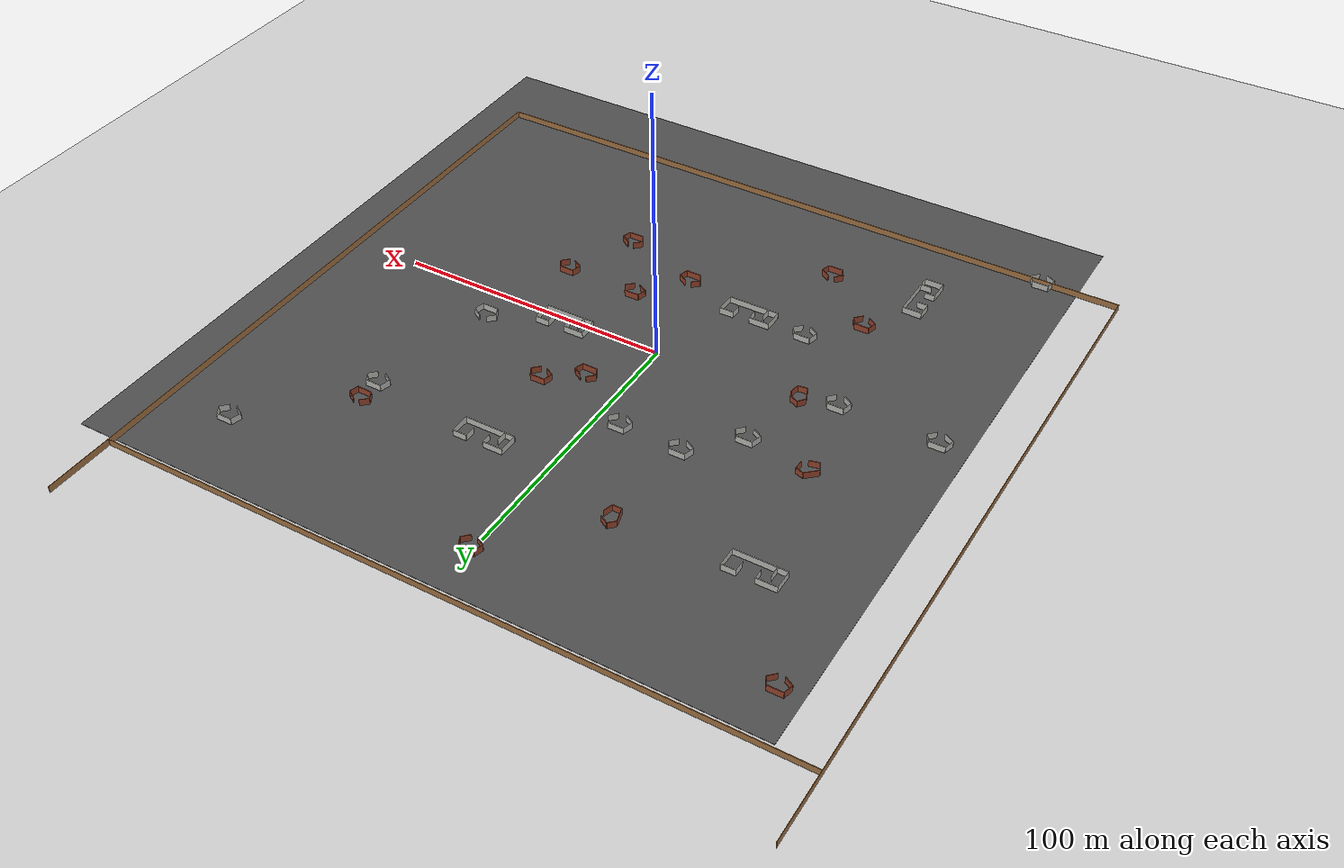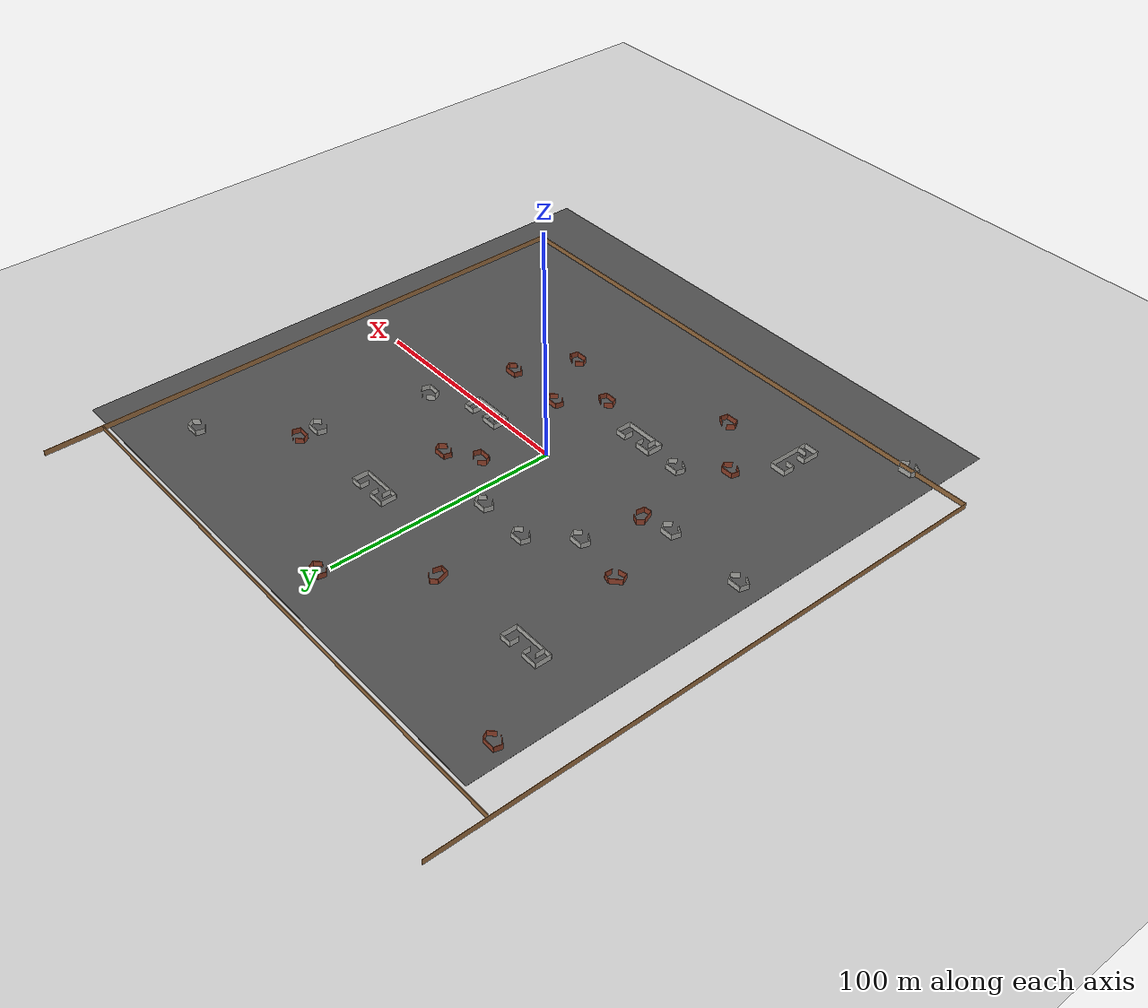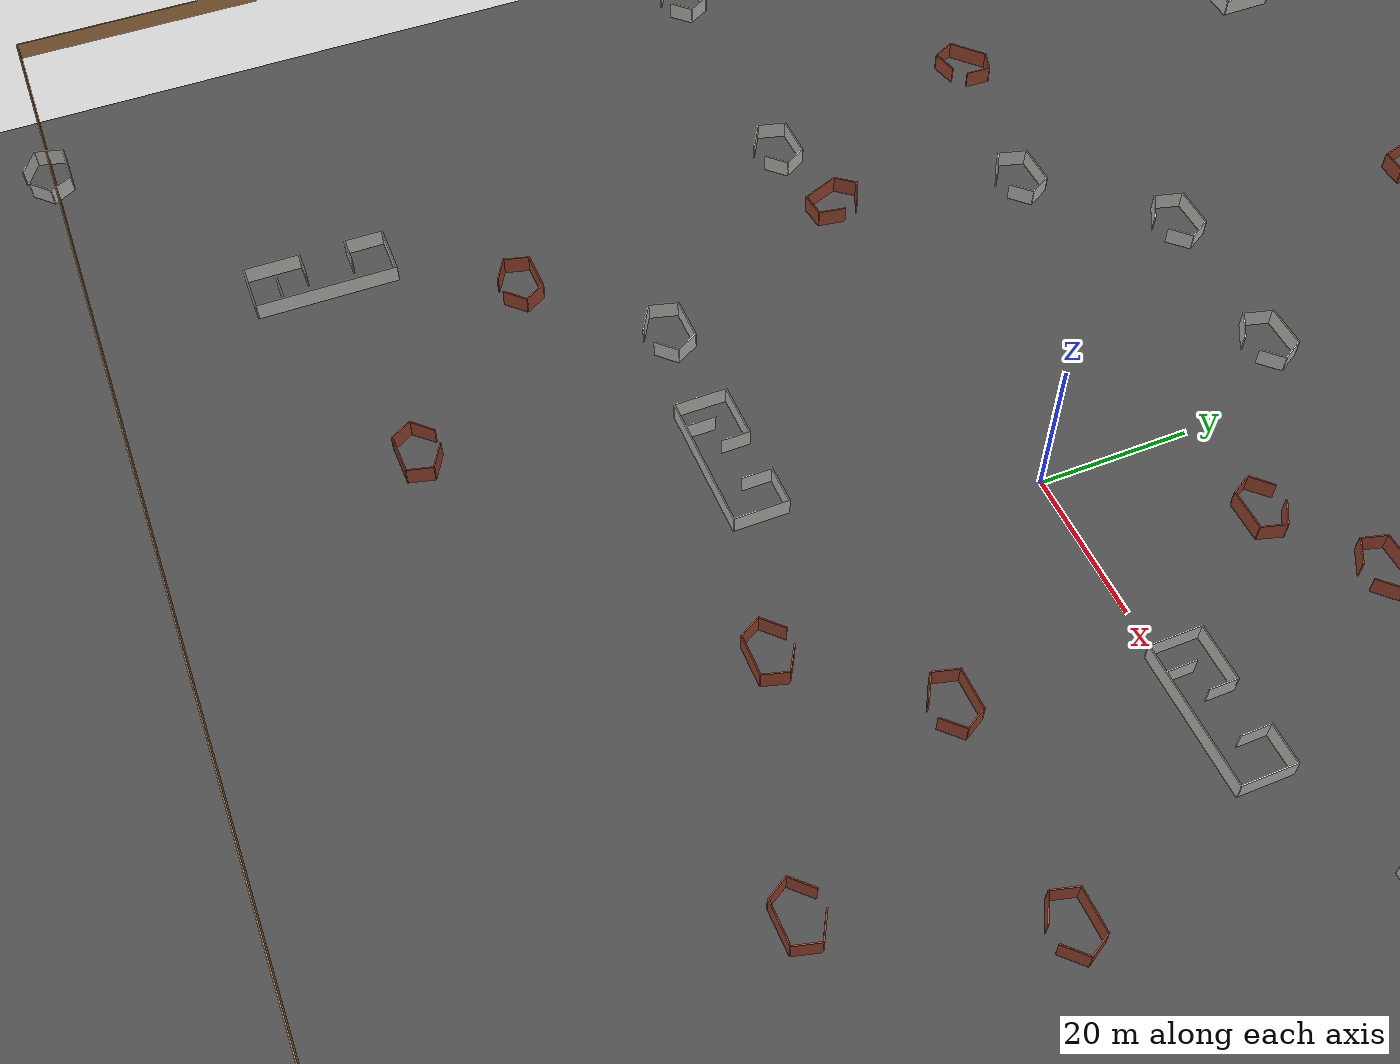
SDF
<sdf version="1.6">
 <world name="default">
  <light name="sun" type="directional">
   <cast_shadows>0</cast_shadows>
   <pose>0 0 10 0 -0 0</pose>
   <diffuse>0.8 0.8 0.8 1</diffuse>
   <specular>0.2 0.2 0.2 1</specular>
   <attenuation>
    <range>1000</range>
    <constant>0.9</constant>
    <linear>0.01</linear>
    <quadratic>0.001</quadratic>
   </attenuation>
   <direction>-0.5 0.1 -0.9</direction>
  </light>
  <model name="ground_plane">
   <static>1</static>
   <link name="link">
    <collision name="collision">
     <geometry><plane><normal>0 0 1</normal><size>250 250</size></plane></geometry>
     <surface><friction><ode><mu>100</mu><mu2>50</mu2></ode></friction></surface>
    </collision>
    <visual name="visual">
     <cast_shadows>0</cast_shadows>
     <geometry><plane><normal>0 0 1</normal><size>250 250</size></plane></geometry>
     <material>
      <script><uri>file://media/materials/scripts/gazebo.material</uri><name>Gazebo/Grey</name></script>
     </material>
    </visual>
   </link>
  </model>
  <plugin name="gazebo_simple_world" filename="libgazebo_simple_world.so"/>
  <physics name="default_physics" default="0" type="ode">
   <max_step_size>0.001</max_step_size>
   <real_time_factor>1</real_time_factor>
   <real_time_update_rate>1000</real_time_update_rate>
  </physics>
  <scene><ambient>0.4 0.4 0.4 1</ambient><background>0.7 0.7 0.7 1</background><shadows>1</shadows></scene>
  <spherical_coordinates>
   <surface_model>EARTH_WGS84</surface_model>
   <latitude_deg>0</latitude_deg>
   <longitude_deg>0</longitude_deg>
   <elevation>0</elevation>
   <heading_deg>0</heading_deg>
  </spherical_coordinates>
  <model name="brick_room1">
   <pose>51.0327 -24.7483 0 0 -0 0</pose>
   <link name="Wall_11">
    <collision name="Wall_11_Collision">
     <geometry><box><size>3.25 0.15 2.5</size></box></geometry>
     <pose>0 0 1.25 0 -0 0</pose>
    </collision>
    <visual name="Wall_11_Visual">
     <pose>0 0 1.25 0 -0 0</pose>
     <geometry><box><size>3.25 0.15 2.5</size></box></geometry>
     <material>
      <script><uri>file://media/materials/scripts/gazebo.material</uri><name>Gazebo/Bricks</name></script>
      <ambient>1 1 1 1</ambient>
     </material>
    </visual>
    <pose>3.12132 1.19483 0 0 0 -1.0472</pose>
   </link>
   <link name="Wall_12">
    <collision name="Wall_12_Collision">
     <geometry><box><size>3.5 0.15 2.5</size></box></geometry>
     <pose>0 0 1.25 0 -0 0</pose>
    </collision>
    <visual name="Wall_12_Visual">
     <pose>0 0 1.25 0 -0 0</pose>
     <geometry><box><size>3.5 0.15 2.5</size></box></geometry>
     <material>
      <script><uri>file://media/materials/scripts/gazebo.material</uri><name>Gazebo/Bricks</name></script>
      <ambient>1 1 1 1</ambient>
     </material>
    </visual>
    <pose>2.71192 -1.33192 0 0 0 -2.35619</pose>
   </link>
   <link name="Wall_7">
    <collision name="Wall_7_Collision">
     <geometry><box><size>5.52935 0.15 2.5</size></box></geometry>
     <pose>0 0 1.25 0 -0 0</pose>
    </collision>
    <visual name="Wall_7_Visual">
     <pose>0 0 1.25 0 -0 0</pose>
     <geometry><box><size>5.52935 0.15 2.5</size></box></geometry>
     <material>
      <script><uri>file://media/materials/scripts/gazebo.material</uri><name>Gazebo/Bricks</name></script>
      <ambient>1 1 1 1</ambient>
     </material>
    </visual>
    <pose>-0.343285 2.51793 0 0 0 -3.13444</pose>
   </link>
   <link name="Wall_8">
    <collision name="Wall_8_Collision">
     <geometry><box><size>3.5 0.15 2.5</size></box></geometry>
     <pose>0 0 1.25 0 -0 0</pose>
    </collision>
    <visual name="Wall_8_Visual">
     <pose>0 0 1.25 0 -0 0</pose>
     <geometry><box><size>3.5 0.15 2.5</size></box></geometry>
     <material>
      <script><uri>file://media/materials/scripts/gazebo.material</uri><name>Gazebo/Bricks</name></script>
      <ambient>1 1 1 1</ambient>
     </material>
    </visual>
    <pose>-3.46641 0.880761 0 0 0 -1.8326</pose>
   </link>
   <link name="Wall_9">
    <collision name="Wall_9_Collision">
     <geometry><box><size>3.75 0.15 2.5</size></box></geometry>
     <pose>0 0 1.25 0 -0 0</pose>
    </collision>
    <visual name="Wall_9_Visual">
     <pose>0 0 1.25 0 -0 0</pose>
     <geometry><box><size>3.75 0.15 2.5</size></box></geometry>
     <material>
      <script><uri>file://media/materials/scripts/gazebo.material</uri><name>Gazebo/Bricks</name></script>
      <ambient>1 1 1 1</ambient>
     </material>
    </visual>
    <pose>-2.34109 -1.63716 0 0 0 -0.523599</pose>
   </link>
   <static>1</static>
  </model>
  <gravity>0 0 -9.8</gravity>
  <magnetic_field>6e-06 2.3e-05 -4.2e-05</magnetic_field>
  <atmosphere type="adiabatic"/>
  <model name="brick_room1_clone">
   <pose>23.7177 -24.224 0 0 -0 0</pose>
   <link name="Wall_11">
    <collision name="Wall_11_Collision">
     <geometry><box><size>3.25 0.15 2.5</size></box></geometry>
     <pose>0 0 1.25 0 -0 0</pose>
    </collision>
    <visual name="Wall_11_Visual">
     <pose>0 0 1.25 0 -0 0</pose>
     <geometry><box><size>3.25 0.15 2.5</size></box></geometry>
     <material>
      <script><uri>file://media/materials/scripts/gazebo.material</uri><name>Gazebo/Bricks</name></script>
      <ambient>1 1 1 1</ambient>
     </material>
    </visual>
    <pose>3.12132 1.19483 0 0 0 -1.0472</pose>
   </link>
   <link name="Wall_12">
    <collision name="Wall_12_Collision">
     <geometry><box><size>3.5 0.15 2.5</size></box></geometry>
     <pose>0 0 1.25 0 -0 0</pose>
    </collision>
    <visual name="Wall_12_Visual">
     <pose>0 0 1.25 0 -0 0</pose>
     <geometry><box><size>3.5 0.15 2.5</size></box></geometry>
     <material>
      <script><uri>file://media/materials/scripts/gazebo.material</uri><name>Gazebo/Bricks</name></script>
      <ambient>1 1 1 1</ambient>
     </material>
    </visual>
    <pose>2.71192 -1.33192 0 0 0 -2.35619</pose>
   </link>
   <link name="Wall_7">
    <collision name="Wall_7_Collision">
     <geometry><box><size>5.52935 0.15 2.5</size></box></geometry>
     <pose>0 0 1.25 0 -0 0</pose>
    </collision>
    <visual name="Wall_7_Visual">
     <pose>0 0 1.25 0 -0 0</pose>
     <geometry><box><size>5.52935 0.15 2.5</size></box></geometry>
     <material>
      <script><uri>file://media/materials/scripts/gazebo.material</uri><name>Gazebo/Bricks</name></script>
      <ambient>1 1 1 1</ambient>
     </material>
    </visual>
    <pose>-0.343285 2.51793 0 0 0 -3.13444</pose>
   </link>
   <link name="Wall_8">
    <collision name="Wall_8_Collision">
     <geometry><box><size>3.5 0.15 2.5</size></box></geometry>
     <pose>0 0 1.25 0 -0 0</pose>
    </collision>
    <visual name="Wall_8_Visual">
     <pose>0 0 1.25 0 -0 0</pose>
     <geometry><box><size>3.5 0.15 2.5</size></box></geometry>
     <material>
      <script><uri>file://media/materials/scripts/gazebo.material</uri><name>Gazebo/Bricks</name></script>
      <ambient>1 1 1 1</ambient>
     </material>
    </visual>
    <pose>-3.46641 0.880761 0 0 0 -1.8326</pose>
   </link>
   <link name="Wall_9">
    <collision name="Wall_9_Collision">
     <geometry><box><size>3.75 0.15 2.5</size></box></geometry>
     <pose>0 0 1.25 0 -0 0</pose>
    </collision>
    <visual name="Wall_9_Visual">
     <pose>0 0 1.25 0 -0 0</pose>
     <geometry><box><size>3.75 0.15 2.5</size></box></geometry>
     <material>
      <script><uri>file://media/materials/scripts/gazebo.material</uri><name>Gazebo/Bricks</name></script>
      <ambient>1 1 1 1</ambient>
     </material>
    </visual>
    <pose>-2.34109 -1.63716 0 0 0 -0.523599</pose>
   </link>
   <static>1</static>
  </model>
  <model name="brick_room1_clone_1">
   <pose>-51.5439 -3.23368 0 0 -0 1.93941</pose>
   <link name="Wall_11">
    <collision name="Wall_11_Collision">
     <geometry><box><size>3.25 0.15 2.5</size></box></geometry>
     <pose>0 0 1.25 0 -0 0</pose>
    </collision>
    <visual name="Wall_11_Visual">
     <pose>0 0 1.25 0 -0 0</pose>
     <geometry><box><size>3.25 0.15 2.5</size></box></geometry>
     <material>
      <script><uri>file://media/materials/scripts/gazebo.material</uri><name>Gazebo/Bricks</name></script>
      <ambient>1 1 1 1</ambient>
     </material>
    </visual>
    <pose>3.12132 1.19483 0 0 0 -1.0472</pose>
   </link>
   <link name="Wall_12">
    <collision name="Wall_12_Collision">
     <geometry><box><size>3.5 0.15 2.5</size></box></geometry>
     <pose>0 0 1.25 0 -0 0</pose>
    </collision>
    <visual name="Wall_12_Visual">
     <pose>0 0 1.25 0 -0 0</pose>
     <geometry><box><size>3.5 0.15 2.5</size></box></geometry>
     <material>
      <script><uri>file://media/materials/scripts/gazebo.material</uri><name>Gazebo/Bricks</name></script>
      <ambient>1 1 1 1</ambient>
     </material>
    </visual>
    <pose>2.71192 -1.33192 0 0 0 -2.35619</pose>
   </link>
   <link name="Wall_7">
    <collision name="Wall_7_Collision">
     <geometry><box><size>5.52935 0.15 2.5</size></box></geometry>
     <pose>0 0 1.25 0 -0 0</pose>
    </collision>
    <visual name="Wall_7_Visual">
     <pose>0 0 1.25 0 -0 0</pose>
     <geometry><box><size>5.52935 0.15 2.5</size></box></geometry>
     <material>
      <script><uri>file://media/materials/scripts/gazebo.material</uri><name>Gazebo/Bricks</name></script>
      <ambient>1 1 1 1</ambient>
     </material>
    </visual>
    <pose>-0.343285 2.51793 0 0 0 -3.13444</pose>
   </link>
   <link name="Wall_8">
    <collision name="Wall_8_Collision">
     <geometry><box><size>3.5 0.15 2.5</size></box></geometry>
     <pose>0 0 1.25 0 -0 0</pose>
    </collision>
    <visual name="Wall_8_Visual">
     <pose>0 0 1.25 0 -0 0</pose>
     <geometry><box><size>3.5 0.15 2.5</size></box></geometry>
     <material>
      <script><uri>file://media/materials/scripts/gazebo.material</uri><name>Gazebo/Bricks</name></script>
      <ambient>1 1 1 1</ambient>
     </material>
    </visual>
    <pose>-3.46641 0.880761 0 0 0 -1.8326</pose>
   </link>
   <link name="Wall_9">
    <collision name="Wall_9_Collision">
     <geometry><box><size>3.75 0.15 2.5</size></box></geometry>
     <pose>0 0 1.25 0 -0 0</pose>
    </collision>
    <visual name="Wall_9_Visual">
     <pose>0 0 1.25 0 -0 0</pose>
     <geometry><box><size>3.75 0.15 2.5</size></box></geometry>
     <material>
      <script><uri>file://media/materials/scripts/gazebo.material</uri><name>Gazebo/Bricks</name></script>
      <ambient>1 1 1 1</ambient>
     </material>
    </visual>
    <pose>-2.34109 -1.63716 0 0 0 -0.523599</pose>
   </link>
   <static>1</static>
  </model>
  <model name="map_frame">
   <pose>0 25 0 0 -0 0</pose>
   <link name="Wall_0">
    <collision name="Wall_0_Collision">
     <geometry><box><size>250.05 0.15 2.5</size></box></geometry>
     <pose>0 0 1.25 0 -0 0</pose>
    </collision>
    <visual name="Wall_0_Visual">
     <pose>0 0 1.25 0 -0 0</pose>
     <geometry><box><size>250.05 0.15 2.5</size></box></geometry>
     <material>
      <script><uri>file://media/materials/scripts/gazebo.material</uri><name>Gazebo/Wood</name></script>
      <ambient>1 1 1 1</ambient>
     </material>
    </visual>
    <pose>0 100 0 0 -0 0</pose>
   </link>
   <link name="Wall_1">
    <collision name="Wall_1_Collision">
     <geometry><box><size>250.05 0.15 2.5</size></box></geometry>
     <pose>0 0 1.25 0 -0 0</pose>
    </collision>
    <visual name="Wall_1_Visual">
     <pose>0 0 1.25 0 -0 0</pose>
     <geometry><box><size>250.05 0.15 2.5</size></box></geometry>
     <material>
      <script><uri>file://media/materials/scripts/gazebo.material</uri><name>Gazebo/Wood</name></script>
      <ambient>1 1 1 1</ambient>
     </material>
    </visual>
    <pose>125 0 0 0 0 -1.5708</pose>
   </link>
   <link name="Wall_2">
    <collision name="Wall_2_Collision">
     <geometry><box><size>250.05 0.15 2.5</size></box></geometry>
     <pose>0 0 1.25 0 -0 0</pose>
    </collision>
    <visual name="Wall_2_Visual">
     <pose>0 0 1.25 0 -0 0</pose>
     <geometry><box><size>250.05 0.15 2.5</size></box></geometry>
     <material>
      <script><uri>file://media/materials/scripts/gazebo.material</uri><name>Gazebo/Wood</name></script>
      <ambient>1 1 1 1</ambient>
     </material>
    </visual>
    <pose>0 -125 0 0 -0 3.14159</pose>
   </link>
   <link name="Wall_3">
    <collision name="Wall_3_Collision">
     <geometry><box><size>250.05 0.15 2.5</size></box></geometry>
     <pose>0 0 1.25 0 -0 0</pose>
    </collision>
    <visual name="Wall_3_Visual">
     <pose>0 0 1.25 0 -0 0</pose>
     <geometry><box><size>250.05 0.15 2.5</size></box></geometry>
     <material>
      <script><uri>file://media/materials/scripts/gazebo.material</uri><name>Gazebo/Wood</name></script>
      <ambient>1 1 1 1</ambient>
     </material>
    </visual>
    <pose>-125 0 0 0 -0 1.5708</pose>
   </link>
   <static>1</static>
  </model>
  <model name="brick_room1_clone_clone">
   <pose>39.6022 -49.4584 0 0 0 -3.13849</pose>
   <link name="Wall_11">
    <collision name="Wall_11_Collision">
     <geometry><box><size>3.25 0.15 2.5</size></box></geometry>
     <pose>0 0 1.25 0 -0 0</pose>
    </collision>
    <visual name="Wall_11_Visual">
     <pose>0 0 1.25 0 -0 0</pose>
     <geometry><box><size>3.25 0.15 2.5</size></box></geometry>
     <material>
      <script><uri>file://media/materials/scripts/gazebo.material</uri><name>Gazebo/Bricks</name></script>
      <ambient>1 1 1 1</ambient>
     </material>
    </visual>
    <pose>3.12132 1.19483 0 0 0 -1.0472</pose>
   </link>
   <link name="Wall_12">
    <collision name="Wall_12_Collision">
     <geometry><box><size>3.5 0.15 2.5</size></box></geometry>
     <pose>0 0 1.25 0 -0 0</pose>
    </collision>
    <visual name="Wall_12_Visual">
     <pose>0 0 1.25 0 -0 0</pose>
     <geometry><box><size>3.5 0.15 2.5</size></box></geometry>
     <material>
      <script><uri>file://media/materials/scripts/gazebo.material</uri><name>Gazebo/Bricks</name></script>
      <ambient>1 1 1 1</ambient>
     </material>
    </visual>
    <pose>2.71192 -1.33192 0 0 0 -2.35619</pose>
   </link>
   <link name="Wall_7">
    <collision name="Wall_7_Collision">
     <geometry><box><size>5.52935 0.15 2.5</size></box></geometry>
     <pose>0 0 1.25 0 -0 0</pose>
    </collision>
    <visual name="Wall_7_Visual">
     <pose>0 0 1.25 0 -0 0</pose>
     <geometry><box><size>5.52935 0.15 2.5</size></box></geometry>
     <material>
      <script><uri>file://media/materials/scripts/gazebo.material</uri><name>Gazebo/Bricks</name></script>
      <ambient>1 1 1 1</ambient>
     </material>
    </visual>
    <pose>-0.343285 2.51793 0 0 0 -3.13444</pose>
   </link>
   <link name="Wall_8">
    <collision name="Wall_8_Collision">
     <geometry><box><size>3.5 0.15 2.5</size></box></geometry>
     <pose>0 0 1.25 0 -0 0</pose>
    </collision>
    <visual name="Wall_8_Visual">
     <pose>0 0 1.25 0 -0 0</pose>
     <geometry><box><size>3.5 0.15 2.5</size></box></geometry>
     <material>
      <script><uri>file://media/materials/scripts/gazebo.material</uri><name>Gazebo/Bricks</name></script>
      <ambient>1 1 1 1</ambient>
     </material>
    </visual>
    <pose>-3.46641 0.880761 0 0 0 -1.8326</pose>
   </link>
   <link name="Wall_9">
    <collision name="Wall_9_Collision">
     <geometry><box><size>3.75 0.15 2.5</size></box></geometry>
     <pose>0 0 1.25 0 -0 0</pose>
    </collision>
    <visual name="Wall_9_Visual">
     <pose>0 0 1.25 0 -0 0</pose>
     <geometry><box><size>3.75 0.15 2.5</size></box></geometry>
     <material>
      <script><uri>file://media/materials/scripts/gazebo.material</uri><name>Gazebo/Bricks</name></script>
      <ambient>1 1 1 1</ambient>
     </material>
    </visual>
    <pose>-2.34109 -1.63716 0 0 0 -0.523599</pose>
   </link>
   <static>1</static>
  </model>
  <model name="brick_room1_clone_clone_0">
   <pose>-28.5109 73.8174 0 0 -0 1.83411</pose>
   <link name="Wall_11">
    <collision name="Wall_11_Collision">
     <geometry><box><size>3.25 0.15 2.5</size></box></geometry>
     <pose>0 0 1.25 0 -0 0</pose>
    </collision>
    <visual name="Wall_11_Visual">
     <pose>0 0 1.25 0 -0 0</pose>
     <geometry><box><size>3.25 0.15 2.5</size></box></geometry>
     <material>
      <script><uri>file://media/materials/scripts/gazebo.material</uri><name>Gazebo/Bricks</name></script>
      <ambient>1 1 1 1</ambient>
     </material>
    </visual>
    <pose>3.12132 1.19483 0 0 0 -1.0472</pose>
   </link>
   <link name="Wall_12">
    <collision name="Wall_12_Collision">
     <geometry><box><size>3.5 0.15 2.5</size></box></geometry>
     <pose>0 0 1.25 0 -0 0</pose>
    </collision>
    <visual name="Wall_12_Visual">
     <pose>0 0 1.25 0 -0 0</pose>
     <geometry><box><size>3.5 0.15 2.5</size></box></geometry>
     <material>
      <script><uri>file://media/materials/scripts/gazebo.material</uri><name>Gazebo/Bricks</name></script>
      <ambient>1 1 1 1</ambient>
     </material>
    </visual>
    <pose>2.71192 -1.33192 0 0 0 -2.35619</pose>
   </link>
   <link name="Wall_7">
    <collision name="Wall_7_Collision">
     <geometry><box><size>5.52935 0.15 2.5</size></box></geometry>
     <pose>0 0 1.25 0 -0 0</pose>
    </collision>
    <visual name="Wall_7_Visual">
     <pose>0 0 1.25 0 -0 0</pose>
     <geometry><box><size>5.52935 0.15 2.5</size></box></geometry>
     <material>
      <script><uri>file://media/materials/scripts/gazebo.material</uri><name>Gazebo/Bricks</name></script>
      <ambient>1 1 1 1</ambient>
     </material>
    </visual>
    <pose>-0.343285 2.51793 0 0 0 -3.13444</pose>
   </link>
   <link name="Wall_8">
    <collision name="Wall_8_Collision">
     <geometry><box><size>3.5 0.15 2.5</size></box></geometry>
     <pose>0 0 1.25 0 -0 0</pose>
    </collision>
    <visual name="Wall_8_Visual">
     <pose>0 0 1.25 0 -0 0</pose>
     <geometry><box><size>3.5 0.15 2.5</size></box></geometry>
     <material>
      <script><uri>file://media/materials/scripts/gazebo.material</uri><name>Gazebo/Bricks</name></script>
      <ambient>1 1 1 1</ambient>
     </material>
    </visual>
    <pose>-3.46641 0.880761 0 0 0 -1.8326</pose>
   </link>
   <link name="Wall_9">
    <collision name="Wall_9_Collision">
     <geometry><box><size>3.75 0.15 2.5</size></box></geometry>
     <pose>0 0 1.25 0 -0 0</pose>
    </collision>
    <visual name="Wall_9_Visual">
     <pose>0 0 1.25 0 -0 0</pose>
     <geometry><box><size>3.75 0.15 2.5</size></box></geometry>
     <material>
      <script><uri>file://media/materials/scripts/gazebo.material</uri><name>Gazebo/Bricks</name></script>
      <ambient>1 1 1 1</ambient>
     </material>
    </visual>
    <pose>-2.34109 -1.63716 0 0 0 -0.523599</pose>
   </link>
   <static>1</static>
  </model>
  <model name="brick_room1_clone_clone_1">
   <pose>-69.8355 25.6563 0 0 -0 0.731826</pose>
   <link name="Wall_11">
    <collision name="Wall_11_Collision">
     <geometry><box><size>3.25 0.15 2.5</size></box></geometry>
     <pose>0 0 1.25 0 -0 0</pose>
    </collision>
    <visual name="Wall_11_Visual">
     <pose>0 0 1.25 0 -0 0</pose>
     <geometry><box><size>3.25 0.15 2.5</size></box></geometry>
     <material>
      <script><uri>file://media/materials/scripts/gazebo.material</uri><name>Gazebo/Bricks</name></script>
      <ambient>1 1 1 1</ambient>
     </material>
    </visual>
    <pose>3.12132 1.19483 0 0 0 -1.0472</pose>
   </link>
   <link name="Wall_12">
    <collision name="Wall_12_Collision">
     <geometry><box><size>3.5 0.15 2.5</size></box></geometry>
     <pose>0 0 1.25 0 -0 0</pose>
    </collision>
    <visual name="Wall_12_Visual">
     <pose>0 0 1.25 0 -0 0</pose>
     <geometry><box><size>3.5 0.15 2.5</size></box></geometry>
     <material>
      <script><uri>file://media/materials/scripts/gazebo.material</uri><name>Gazebo/Bricks</name></script>
      <ambient>1 1 1 1</ambient>
     </material>
    </visual>
    <pose>2.71192 -1.33192 0 0 0 -2.35619</pose>
   </link>
   <link name="Wall_7">
    <collision name="Wall_7_Collision">
     <geometry><box><size>5.52935 0.15 2.5</size></box></geometry>
     <pose>0 0 1.25 0 -0 0</pose>
    </collision>
    <visual name="Wall_7_Visual">
     <pose>0 0 1.25 0 -0 0</pose>
     <geometry><box><size>5.52935 0.15 2.5</size></box></geometry>
     <material>
      <script><uri>file://media/materials/scripts/gazebo.material</uri><name>Gazebo/Bricks</name></script>
      <ambient>1 1 1 1</ambient>
     </material>
    </visual>
    <pose>-0.343285 2.51793 0 0 0 -3.13444</pose>
   </link>
   <link name="Wall_8">
    <collision name="Wall_8_Collision">
     <geometry><box><size>3.5 0.15 2.5</size></box></geometry>
     <pose>0 0 1.25 0 -0 0</pose>
    </collision>
    <visual name="Wall_8_Visual">
     <pose>0 0 1.25 0 -0 0</pose>
     <geometry><box><size>3.5 0.15 2.5</size></box></geometry>
     <material>
      <script><uri>file://media/materials/scripts/gazebo.material</uri><name>Gazebo/Bricks</name></script>
      <ambient>1 1 1 1</ambient>
     </material>
    </visual>
    <pose>-3.46641 0.880761 0 0 0 -1.8326</pose>
   </link>
   <link name="Wall_9">
    <collision name="Wall_9_Collision">
     <geometry><box><size>3.75 0.15 2.5</size></box></geometry>
     <pose>0 0 1.25 0 -0 0</pose>
    </collision>
    <visual name="Wall_9_Visual">
     <pose>0 0 1.25 0 -0 0</pose>
     <geometry><box><size>3.75 0.15 2.5</size></box></geometry>
     <material>
      <script><uri>file://media/materials/scripts/gazebo.material</uri><name>Gazebo/Bricks</name></script>
      <ambient>1 1 1 1</ambient>
     </material>
    </visual>
    <pose>-2.34109 -1.63716 0 0 0 -0.523599</pose>
   </link>
   <static>1</static>
  </model>
  <model name="concrete_room2">
   <pose>-16.6663 -33.2911 0 0 -0 0</pose>
   <link name="Wall_61">
    <collision name="Wall_61_Collision">
     <geometry><box><size>5.25 0.15 2.5</size></box></geometry>
     <pose>0 0 1.25 0 -0 0</pose>
    </collision>
    <visual name="Wall_61_Visual">
     <pose>0 0 1.25 0 -0 0</pose>
     <geometry><box><size>5.25 0.15 2.5</size></box></geometry>
     <material>
      <script><uri>file://media/materials/scripts/gazebo.material</uri><name>Gazebo/CeilingTiled</name></script>
      <ambient>1 1 1 1</ambient>
     </material>
     <meta><layer>0</layer></meta>
    </visual>
    <pose>6.75 3.55 0 0 -0 0</pose>
   </link>
   <link name="Wall_62">
    <collision name="Wall_62_Collision">
     <geometry><box><size>7.25 0.15 2.5</size></box></geometry>
     <pose>0 0 1.25 0 -0 0</pose>
    </collision>
    <visual name="Wall_62_Visual">
     <pose>0 0 1.25 0 -0 0</pose>
     <geometry><box><size>7.25 0.15 2.5</size></box></geometry>
     <material>
      <script><uri>file://media/materials/scripts/gazebo.material</uri><name>Gazebo/CeilingTiled</name></script>
      <ambient>1 1 1 1</ambient>
     </material>
     <meta><layer>0</layer></meta>
    </visual>
    <pose>9.3 0 0 0 0 -1.5708</pose>
   </link>
   <link name="Wall_63">
    <collision name="Wall_63_Collision">
     <geometry><box><size>18.75 0.15 2.5</size></box></geometry>
     <pose>0 0 1.25 0 -0 0</pose>
    </collision>
    <visual name="Wall_63_Visual">
     <pose>0 0 1.25 0 -0 0</pose>
     <geometry><box><size>18.75 0.15 2.5</size></box></geometry>
     <material>
      <script><uri>file://media/materials/scripts/gazebo.material</uri><name>Gazebo/CeilingTiled</name></script>
      <ambient>1 1 1 1</ambient>
     </material>
     <meta><layer>0</layer></meta>
    </visual>
    <pose>0 -3.55 0 0 -0 3.14159</pose>
   </link>
   <link name="Wall_64">
    <collision name="Wall_64_Collision">
     <geometry><box><size>7 0.15 2.5</size></box></geometry>
     <pose>0 0 1.25 0 -0 0</pose>
    </collision>
    <visual name="Wall_64_Visual">
     <pose>0 0 1.25 0 -0 0</pose>
     <geometry><box><size>7 0.15 2.5</size></box></geometry>
     <material>
      <script><uri>file://media/materials/scripts/gazebo.material</uri><name>Gazebo/CeilingTiled</name></script>
      <ambient>1 1 1 1</ambient>
     </material>
     <meta><layer>0</layer></meta>
    </visual>
    <pose>-9.3 -0.125 0 0 -0 1.5708</pose>
   </link>
   <link name="Wall_65">
    <collision name="Wall_65_Collision">
     <geometry><box><size>7.5 0.15 2.5</size></box></geometry>
     <pose>0 0 1.25 0 -0 0</pose>
    </collision>
    <visual name="Wall_65_Visual">
     <pose>0 0 1.25 0 -0 0</pose>
     <geometry><box><size>7.5 0.15 2.5</size></box></geometry>
     <material>
      <script><uri>file://media/materials/scripts/gazebo.material</uri><name>Gazebo/CeilingTiled</name></script>
      <ambient>1 1 1 1</ambient>
     </material>
     <meta><layer>0</layer></meta>
    </visual>
    <pose>-5.625 3.3 0 0 -0 0</pose>
   </link>
   <link name="Wall_66">
    <collision name="Wall_66_Collision">
     <geometry><box><size>3.75 0.15 2.5</size></box></geometry>
     <pose>0 0 1.25 0 -0 0</pose>
    </collision>
    <visual name="Wall_66_Visual">
     <pose>0 0 1.25 0 -0 0</pose>
     <geometry><box><size>3.75 0.15 2.5</size></box></geometry>
     <material>
      <script><uri>file://media/materials/scripts/gazebo.material</uri><name>Gazebo/CeilingTiled</name></script>
      <ambient>1 1 1 1</ambient>
     </material>
     <meta><layer>0</layer></meta>
    </visual>
    <pose>-1.95 1.5 0 0 0 -1.5708</pose>
   </link>
   <link name="Wall_70">
    <collision name="Wall_70_Collision">
     <geometry><box><size>4 0.15 2.5</size></box></geometry>
     <pose>0 0 1.25 0 -0 0</pose>
    </collision>
    <visual name="Wall_70_Visual">
     <pose>0 0 1.25 0 -0 0</pose>
     <geometry><box><size>4 0.15 2.5</size></box></geometry>
     <material>
      <script><uri>file://media/materials/scripts/gazebo.material</uri><name>Gazebo/CeilingTiled</name></script>
      <ambient>1 1 1 1</ambient>
     </material>
     <meta><layer>0</layer></meta>
    </visual>
    <pose>4.2 1.625 0 0 0 -1.5708</pose>
   </link>
   <link name="Wall_72">
    <collision name="Wall_72_Collision">
     <geometry><box><size>4 0.15 2.5</size></box></geometry>
     <pose>0 0 1.25 0 -0 0</pose>
    </collision>
    <visual name="Wall_72_Visual">
     <pose>0 0 1.25 0 -0 0</pose>
     <geometry><box><size>4 0.15 2.5</size></box></geometry>
     <material>
      <script><uri>file://media/materials/scripts/gazebo.material</uri><name>Gazebo/CeilingTiled</name></script>
      <ambient>1 1 1 1</ambient>
     </material>
     <meta><layer>0</layer></meta>
    </visual>
    <pose>-5.65005 -1.59593 0 0 -0 1.5708</pose>
   </link>
   <static>1</static>
  </model>
  <model name="concrete_room2_0">
   <pose>-64.8929 -70.9047 0 0 -0 1.56011</pose>
   <link name="Wall_61">
    <collision name="Wall_61_Collision">
     <geometry><box><size>5.25 0.15 2.5</size></box></geometry>
     <pose>0 0 1.25 0 -0 0</pose>
    </collision>
    <visual name="Wall_61_Visual">
     <pose>0 0 1.25 0 -0 0</pose>
     <geometry><box><size>5.25 0.15 2.5</size></box></geometry>
     <material>
      <script><uri>file://media/materials/scripts/gazebo.material</uri><name>Gazebo/CeilingTiled</name></script>
      <ambient>1 1 1 1</ambient>
     </material>
     <meta><layer>0</layer></meta>
    </visual>
    <pose>6.75 3.55 0 0 -0 0</pose>
   </link>
   <link name="Wall_62">
    <collision name="Wall_62_Collision">
     <geometry><box><size>7.25 0.15 2.5</size></box></geometry>
     <pose>0 0 1.25 0 -0 0</pose>
    </collision>
    <visual name="Wall_62_Visual">
     <pose>0 0 1.25 0 -0 0</pose>
     <geometry><box><size>7.25 0.15 2.5</size></box></geometry>
     <material>
      <script><uri>file://media/materials/scripts/gazebo.material</uri><name>Gazebo/CeilingTiled</name></script>
      <ambient>1 1 1 1</ambient>
     </material>
     <meta><layer>0</layer></meta>
    </visual>
    <pose>9.3 0 0 0 0 -1.5708</pose>
   </link>
   <link name="Wall_63">
    <collision name="Wall_63_Collision">
     <geometry><box><size>18.75 0.15 2.5</size></box></geometry>
     <pose>0 0 1.25 0 -0 0</pose>
    </collision>
    <visual name="Wall_63_Visual">
     <pose>0 0 1.25 0 -0 0</pose>
     <geometry><box><size>18.75 0.15 2.5</size></box></geometry>
     <material>
      <script><uri>file://media/materials/scripts/gazebo.material</uri><name>Gazebo/CeilingTiled</name></script>
      <ambient>1 1 1 1</ambient>
     </material>
     <meta><layer>0</layer></meta>
    </visual>
    <pose>0 -3.55 0 0 -0 3.14159</pose>
   </link>
   <link name="Wall_64">
    <collision name="Wall_64_Collision">
     <geometry><box><size>7 0.15 2.5</size></box></geometry>
     <pose>0 0 1.25 0 -0 0</pose>
    </collision>
    <visual name="Wall_64_Visual">
     <pose>0 0 1.25 0 -0 0</pose>
     <geometry><box><size>7 0.15 2.5</size></box></geometry>
     <material>
      <script><uri>file://media/materials/scripts/gazebo.material</uri><name>Gazebo/CeilingTiled</name></script>
      <ambient>1 1 1 1</ambient>
     </material>
     <meta><layer>0</layer></meta>
    </visual>
    <pose>-9.3 -0.125 0 0 -0 1.5708</pose>
   </link>
   <link name="Wall_65">
    <collision name="Wall_65_Collision">
     <geometry><box><size>7.5 0.15 2.5</size></box></geometry>
     <pose>0 0 1.25 0 -0 0</pose>
    </collision>
    <visual name="Wall_65_Visual">
     <pose>0 0 1.25 0 -0 0</pose>
     <geometry><box><size>7.5 0.15 2.5</size></box></geometry>
     <material>
      <script><uri>file://media/materials/scripts/gazebo.material</uri><name>Gazebo/CeilingTiled</name></script>
      <ambient>1 1 1 1</ambient>
     </material>
     <meta><layer>0</layer></meta>
    </visual>
    <pose>-5.625 3.3 0 0 -0 0</pose>
   </link>
   <link name="Wall_66">
    <collision name="Wall_66_Collision">
     <geometry><box><size>3.75 0.15 2.5</size></box></geometry>
     <pose>0 0 1.25 0 -0 0</pose>
    </collision>
    <visual name="Wall_66_Visual">
     <pose>0 0 1.25 0 -0 0</pose>
     <geometry><box><size>3.75 0.15 2.5</size></box></geometry>
     <material>
      <script><uri>file://media/materials/scripts/gazebo.material</uri><name>Gazebo/CeilingTiled</name></script>
      <ambient>1 1 1 1</ambient>
     </material>
     <meta><layer>0</layer></meta>
    </visual>
    <pose>-1.95 1.5 0 0 0 -1.5708</pose>
   </link>
   <link name="Wall_70">
    <collision name="Wall_70_Collision">
     <geometry><box><size>4 0.15 2.5</size></box></geometry>
     <pose>0 0 1.25 0 -0 0</pose>
    </collision>
    <visual name="Wall_70_Visual">
     <pose>0 0 1.25 0 -0 0</pose>
     <geometry><box><size>4 0.15 2.5</size></box></geometry>
     <material>
      <script><uri>file://media/materials/scripts/gazebo.material</uri><name>Gazebo/CeilingTiled</name></script>
      <ambient>1 1 1 1</ambient>
     </material>
     <meta><layer>0</layer></meta>
    </visual>
    <pose>4.2 1.625 0 0 0 -1.5708</pose>
   </link>
   <link name="Wall_72">
    <collision name="Wall_72_Collision">
     <geometry><box><size>4 0.15 2.5</size></box></geometry>
     <pose>0 0 1.25 0 -0 0</pose>
    </collision>
    <visual name="Wall_72_Visual">
     <pose>0 0 1.25 0 -0 0</pose>
     <geometry><box><size>4 0.15 2.5</size></box></geometry>
     <material>
      <script><uri>file://media/materials/scripts/gazebo.material</uri><name>Gazebo/CeilingTiled</name></script>
      <ambient>1 1 1 1</ambient>
     </material>
     <meta><layer>0</layer></meta>
    </visual>
    <pose>-5.65005 -1.59593 0 0 -0 1.5708</pose>
   </link>
   <static>1</static>
  </model>
  <model name="concrete_room2_1">
   <pose>25.2761 63.5704 0 0 -0 0</pose>
   <link name="Wall_61">
    <collision name="Wall_61_Collision">
     <geometry><box><size>5.25 0.15 2.5</size></box></geometry>
     <pose>0 0 1.25 0 -0 0</pose>
    </collision>
    <visual name="Wall_61_Visual">
     <pose>0 0 1.25 0 -0 0</pose>
     <geometry><box><size>5.25 0.15 2.5</size></box></geometry>
     <material>
      <script><uri>file://media/materials/scripts/gazebo.material</uri><name>Gazebo/CeilingTiled</name></script>
      <ambient>1 1 1 1</ambient>
     </material>
     <meta><layer>0</layer></meta>
    </visual>
    <pose>6.75 3.55 0 0 -0 0</pose>
   </link>
   <link name="Wall_62">
    <collision name="Wall_62_Collision">
     <geometry><box><size>7.25 0.15 2.5</size></box></geometry>
     <pose>0 0 1.25 0 -0 0</pose>
    </collision>
    <visual name="Wall_62_Visual">
     <pose>0 0 1.25 0 -0 0</pose>
     <geometry><box><size>7.25 0.15 2.5</size></box></geometry>
     <material>
      <script><uri>file://media/materials/scripts/gazebo.material</uri><name>Gazebo/CeilingTiled</name></script>
      <ambient>1 1 1 1</ambient>
     </material>
     <meta><layer>0</layer></meta>
    </visual>
    <pose>9.3 0 0 0 0 -1.5708</pose>
   </link>
   <link name="Wall_63">
    <collision name="Wall_63_Collision">
     <geometry><box><size>18.75 0.15 2.5</size></box></geometry>
     <pose>0 0 1.25 0 -0 0</pose>
    </collision>
    <visual name="Wall_63_Visual">
     <pose>0 0 1.25 0 -0 0</pose>
     <geometry><box><size>18.75 0.15 2.5</size></box></geometry>
     <material>
      <script><uri>file://media/materials/scripts/gazebo.material</uri><name>Gazebo/CeilingTiled</name></script>
      <ambient>1 1 1 1</ambient>
     </material>
     <meta><layer>0</layer></meta>
    </visual>
    <pose>0 -3.55 0 0 -0 3.14159</pose>
   </link>
   <link name="Wall_64">
    <collision name="Wall_64_Collision">
     <geometry><box><size>7 0.15 2.5</size></box></geometry>
     <pose>0 0 1.25 0 -0 0</pose>
    </collision>
    <visual name="Wall_64_Visual">
     <pose>0 0 1.25 0 -0 0</pose>
     <geometry><box><size>7 0.15 2.5</size></box></geometry>
     <material>
      <script><uri>file://media/materials/scripts/gazebo.material</uri><name>Gazebo/CeilingTiled</name></script>
      <ambient>1 1 1 1</ambient>
     </material>
     <meta><layer>0</layer></meta>
    </visual>
    <pose>-9.3 -0.125 0 0 -0 1.5708</pose>
   </link>
   <link name="Wall_65">
    <collision name="Wall_65_Collision">
     <geometry><box><size>7.5 0.15 2.5</size></box></geometry>
     <pose>0 0 1.25 0 -0 0</pose>
    </collision>
    <visual name="Wall_65_Visual">
     <pose>0 0 1.25 0 -0 0</pose>
     <geometry><box><size>7.5 0.15 2.5</size></box></geometry>
     <material>
      <script><uri>file://media/materials/scripts/gazebo.material</uri><name>Gazebo/CeilingTiled</name></script>
      <ambient>1 1 1 1</ambient>
     </material>
     <meta><layer>0</layer></meta>
    </visual>
    <pose>-5.625 3.3 0 0 -0 0</pose>
   </link>
   <link name="Wall_66">
    <collision name="Wall_66_Collision">
     <geometry><box><size>3.75 0.15 2.5</size></box></geometry>
     <pose>0 0 1.25 0 -0 0</pose>
    </collision>
    <visual name="Wall_66_Visual">
     <pose>0 0 1.25 0 -0 0</pose>
     <geometry><box><size>3.75 0.15 2.5</size></box></geometry>
     <material>
      <script><uri>file://media/materials/scripts/gazebo.material</uri><name>Gazebo/CeilingTiled</name></script>
      <ambient>1 1 1 1</ambient>
     </material>
     <meta><layer>0</layer></meta>
    </visual>
    <pose>-1.95 1.5 0 0 0 -1.5708</pose>
   </link>
   <link name="Wall_70">
    <collision name="Wall_70_Collision">
     <geometry><box><size>4 0.15 2.5</size></box></geometry>
     <pose>0 0 1.25 0 -0 0</pose>
    </collision>
    <visual name="Wall_70_Visual">
     <pose>0 0 1.25 0 -0 0</pose>
     <geometry><box><size>4 0.15 2.5</size></box></geometry>
     <material>
      <script><uri>file://media/materials/scripts/gazebo.material</uri><name>Gazebo/CeilingTiled</name></script>
      <ambient>1 1 1 1</ambient>
     </material>
     <meta><layer>0</layer></meta>
    </visual>
    <pose>4.2 1.625 0 0 0 -1.5708</pose>
   </link>
   <link name="Wall_72">
    <collision name="Wall_72_Collision">
     <geometry><box><size>4 0.15 2.5</size></box></geometry>
     <pose>0 0 1.25 0 -0 0</pose>
    </collision>
    <visual name="Wall_72_Visual">
     <pose>0 0 1.25 0 -0 0</pose>
     <geometry><box><size>4 0.15 2.5</size></box></geometry>
     <material>
      <script><uri>file://media/materials/scripts/gazebo.material</uri><name>Gazebo/CeilingTiled</name></script>
      <ambient>1 1 1 1</ambient>
     </material>
     <meta><layer>0</layer></meta>
    </visual>
    <pose>-5.65005 -1.59593 0 0 -0 1.5708</pose>
   </link>
   <static>1</static>
  </model>
  <model name="concrete_room2_2">
   <pose>35.246 2.40553 0 0 -0 0</pose>
   <link name="Wall_61">
    <collision name="Wall_61_Collision">
     <geometry><box><size>5.25 0.15 2.5</size></box></geometry>
     <pose>0 0 1.25 0 -0 0</pose>
    </collision>
    <visual name="Wall_61_Visual">
     <pose>0 0 1.25 0 -0 0</pose>
     <geometry><box><size>5.25 0.15 2.5</size></box></geometry>
     <material>
      <script><uri>file://media/materials/scripts/gazebo.material</uri><name>Gazebo/CeilingTiled</name></script>
      <ambient>1 1 1 1</ambient>
     </material>
     <meta><layer>0</layer></meta>
    </visual>
    <pose>6.75 3.55 0 0 -0 0</pose>
   </link>
   <link name="Wall_62">
    <collision name="Wall_62_Collision">
     <geometry><box><size>7.25 0.15 2.5</size></box></geometry>
     <pose>0 0 1.25 0 -0 0</pose>
    </collision>
    <visual name="Wall_62_Visual">
     <pose>0 0 1.25 0 -0 0</pose>
     <geometry><box><size>7.25 0.15 2.5</size></box></geometry>
     <material>
      <script><uri>file://media/materials/scripts/gazebo.material</uri><name>Gazebo/CeilingTiled</name></script>
      <ambient>1 1 1 1</ambient>
     </material>
     <meta><layer>0</layer></meta>
    </visual>
    <pose>9.3 0 0 0 0 -1.5708</pose>
   </link>
   <link name="Wall_63">
    <collision name="Wall_63_Collision">
     <geometry><box><size>18.75 0.15 2.5</size></box></geometry>
     <pose>0 0 1.25 0 -0 0</pose>
    </collision>
    <visual name="Wall_63_Visual">
     <pose>0 0 1.25 0 -0 0</pose>
     <geometry><box><size>18.75 0.15 2.5</size></box></geometry>
     <material>
      <script><uri>file://media/materials/scripts/gazebo.material</uri><name>Gazebo/CeilingTiled</name></script>
      <ambient>1 1 1 1</ambient>
     </material>
     <meta><layer>0</layer></meta>
    </visual>
    <pose>0 -3.55 0 0 -0 3.14159</pose>
   </link>
   <link name="Wall_64">
    <collision name="Wall_64_Collision">
     <geometry><box><size>7 0.15 2.5</size></box></geometry>
     <pose>0 0 1.25 0 -0 0</pose>
    </collision>
    <visual name="Wall_64_Visual">
     <pose>0 0 1.25 0 -0 0</pose>
     <geometry><box><size>7 0.15 2.5</size></box></geometry>
     <material>
      <script><uri>file://media/materials/scripts/gazebo.material</uri><name>Gazebo/CeilingTiled</name></script>
      <ambient>1 1 1 1</ambient>
     </material>
     <meta><layer>0</layer></meta>
    </visual>
    <pose>-9.3 -0.125 0 0 -0 1.5708</pose>
   </link>
   <link name="Wall_65">
    <collision name="Wall_65_Collision">
     <geometry><box><size>7.5 0.15 2.5</size></box></geometry>
     <pose>0 0 1.25 0 -0 0</pose>
    </collision>
    <visual name="Wall_65_Visual">
     <pose>0 0 1.25 0 -0 0</pose>
     <geometry><box><size>7.5 0.15 2.5</size></box></geometry>
     <material>
      <script><uri>file://media/materials/scripts/gazebo.material</uri><name>Gazebo/CeilingTiled</name></script>
      <ambient>1 1 1 1</ambient>
     </material>
     <meta><layer>0</layer></meta>
    </visual>
    <pose>-5.625 3.3 0 0 -0 0</pose>
   </link>
   <link name="Wall_66">
    <collision name="Wall_66_Collision">
     <geometry><box><size>3.75 0.15 2.5</size></box></geometry>
     <pose>0 0 1.25 0 -0 0</pose>
    </collision>
    <visual name="Wall_66_Visual">
     <pose>0 0 1.25 0 -0 0</pose>
     <geometry><box><size>3.75 0.15 2.5</size></box></geometry>
     <material>
      <script><uri>file://media/materials/scripts/gazebo.material</uri><name>Gazebo/CeilingTiled</name></script>
      <ambient>1 1 1 1</ambient>
     </material>
     <meta><layer>0</layer></meta>
    </visual>
    <pose>-1.95 1.5 0 0 0 -1.5708</pose>
   </link>
   <link name="Wall_70">
    <collision name="Wall_70_Collision">
     <geometry><box><size>4 0.15 2.5</size></box></geometry>
     <pose>0 0 1.25 0 -0 0</pose>
    </collision>
    <visual name="Wall_70_Visual">
     <pose>0 0 1.25 0 -0 0</pose>
     <geometry><box><size>4 0.15 2.5</size></box></geometry>
     <material>
      <script><uri>file://media/materials/scripts/gazebo.material</uri><name>Gazebo/CeilingTiled</name></script>
      <ambient>1 1 1 1</ambient>
     </material>
     <meta><layer>0</layer></meta>
    </visual>
    <pose>4.2 1.625 0 0 0 -1.5708</pose>
   </link>
   <link name="Wall_72">
    <collision name="Wall_72_Collision">
     <geometry><box><size>4 0.15 2.5</size></box></geometry>
     <pose>0 0 1.25 0 -0 0</pose>
    </collision>
    <visual name="Wall_72_Visual">
     <pose>0 0 1.25 0 -0 0</pose>
     <geometry><box><size>4 0.15 2.5</size></box></geometry>
     <material>
      <script><uri>file://media/materials/scripts/gazebo.material</uri><name>Gazebo/CeilingTiled</name></script>
      <ambient>1 1 1 1</ambient>
     </material>
     <meta><layer>0</layer></meta>
    </visual>
    <pose>-5.65005 -1.59593 0 0 -0 1.5708</pose>
   </link>
   <static>1</static>
  </model>
  <model name="concrete_room">
   <pose>-64.1032 -6.51639 0 0 -0 0</pose>
   <link name="Wall_54">
    <collision name="Wall_54_Collision">
     <geometry><box><size>4.25 0.15 2.5</size></box></geometry>
     <pose>0 0 1.25 0 -0 0</pose>
    </collision>
    <visual name="Wall_54_Visual">
     <pose>0 0 1.25 0 -0 0</pose>
     <geometry><box><size>4.25 0.15 2.5</size></box></geometry>
     <material>
      <script><uri>file://media/materials/scripts/gazebo.material</uri><name>Gazebo/CeilingTiled</name></script>
      <ambient>1 1 1 1</ambient>
     </material>
     <meta><layer>0</layer></meta>
    </visual>
    <pose>-2.48718 -1.85941 0 0 -0 2.61799</pose>
   </link>
   <link name="Wall_55">
    <collision name="Wall_55_Collision">
     <geometry><box><size>4 0.15 2.5</size></box></geometry>
     <pose>0 0 1.25 0 -0 0</pose>
    </collision>
    <visual name="Wall_55_Visual">
     <pose>0 0 1.25 0 -0 0</pose>
     <geometry><box><size>4 0.15 2.5</size></box></geometry>
     <material>
      <script><uri>file://media/materials/scripts/gazebo.material</uri><name>Gazebo/CeilingTiled</name></script>
      <ambient>1 1 1 1</ambient>
     </material>
     <meta><layer>0</layer></meta>
    </visual>
    <pose>-3.76431 1.025 0 0 -0 1.309</pose>
   </link>
   <link name="Wall_56">
    <collision name="Wall_56_Collision">
     <geometry><box><size>6 0.15 2.5</size></box></geometry>
     <pose>0 0 1.25 0 -0 0</pose>
    </collision>
    <visual name="Wall_56_Visual">
     <pose>0 0 1.25 0 -0 0</pose>
     <geometry><box><size>6 0.15 2.5</size></box></geometry>
     <material>
      <script><uri>file://media/materials/scripts/gazebo.material</uri><name>Gazebo/CeilingTiled</name></script>
      <ambient>1 1 1 1</ambient>
     </material>
     <meta><layer>0</layer></meta>
    </visual>
    <pose>-0.34108 2.88441 0 0 -0 0</pose>
   </link>
   <link name="Wall_57">
    <collision name="Wall_57_Collision">
     <geometry><box><size>3.5 0.15 2.5</size></box></geometry>
     <pose>0 0 1.25 0 -0 0</pose>
    </collision>
    <visual name="Wall_57_Visual">
     <pose>0 0 1.25 0 -0 0</pose>
     <geometry><box><size>3.5 0.15 2.5</size></box></geometry>
     <material>
      <script><uri>file://media/materials/scripts/gazebo.material</uri><name>Gazebo/CeilingTiled</name></script>
      <ambient>1 1 1 1</ambient>
     </material>
     <meta><layer>0</layer></meta>
    </visual>
    <pose>3.42142 1.43382 0 0 0 -1.0472</pose>
   </link>
   <link name="Wall_58">
    <collision name="Wall_58_Collision">
     <geometry><box><size>3.5 0.15 2.5</size></box></geometry>
     <pose>0 0 1.25 0 -0 0</pose>
    </collision>
    <visual name="Wall_58_Visual">
     <pose>0 0 1.25 0 -0 0</pose>
     <geometry><box><size>3.5 0.15 2.5</size></box></geometry>
     <material>
      <script><uri>file://media/materials/scripts/gazebo.material</uri><name>Gazebo/CeilingTiled</name></script>
      <ambient>1 1 1 1</ambient>
     </material>
     <meta><layer>0</layer></meta>
    </visual>
    <pose>3.07452 -1.20118 0 0 0 -2.35619</pose>
   </link>
   <static>1</static>
  </model>
  <model name="concrete_room_0">
   <pose>-38.2555 -32.9617 0 0 -0 0</pose>
   <link name="Wall_54">
    <collision name="Wall_54_Collision">
     <geometry><box><size>4.25 0.15 2.5</size></box></geometry>
     <pose>0 0 1.25 0 -0 0</pose>
    </collision>
    <visual name="Wall_54_Visual">
     <pose>0 0 1.25 0 -0 0</pose>
     <geometry><box><size>4.25 0.15 2.5</size></box></geometry>
     <material>
      <script><uri>file://media/materials/scripts/gazebo.material</uri><name>Gazebo/CeilingTiled</name></script>
      <ambient>1 1 1 1</ambient>
     </material>
     <meta><layer>0</layer></meta>
    </visual>
    <pose>-2.48718 -1.85941 0 0 -0 2.61799</pose>
   </link>
   <link name="Wall_55">
    <collision name="Wall_55_Collision">
     <geometry><box><size>4 0.15 2.5</size></box></geometry>
     <pose>0 0 1.25 0 -0 0</pose>
    </collision>
    <visual name="Wall_55_Visual">
     <pose>0 0 1.25 0 -0 0</pose>
     <geometry><box><size>4 0.15 2.5</size></box></geometry>
     <material>
      <script><uri>file://media/materials/scripts/gazebo.material</uri><name>Gazebo/CeilingTiled</name></script>
      <ambient>1 1 1 1</ambient>
     </material>
     <meta><layer>0</layer></meta>
    </visual>
    <pose>-3.76431 1.025 0 0 -0 1.309</pose>
   </link>
   <link name="Wall_56">
    <collision name="Wall_56_Collision">
     <geometry><box><size>6 0.15 2.5</size></box></geometry>
     <pose>0 0 1.25 0 -0 0</pose>
    </collision>
    <visual name="Wall_56_Visual">
     <pose>0 0 1.25 0 -0 0</pose>
     <geometry><box><size>6 0.15 2.5</size></box></geometry>
     <material>
      <script><uri>file://media/materials/scripts/gazebo.material</uri><name>Gazebo/CeilingTiled</name></script>
      <ambient>1 1 1 1</ambient>
     </material>
     <meta><layer>0</layer></meta>
    </visual>
    <pose>-0.34108 2.88441 0 0 -0 0</pose>
   </link>
   <link name="Wall_57">
    <collision name="Wall_57_Collision">
     <geometry><box><size>3.5 0.15 2.5</size></box></geometry>
     <pose>0 0 1.25 0 -0 0</pose>
    </collision>
    <visual name="Wall_57_Visual">
     <pose>0 0 1.25 0 -0 0</pose>
     <geometry><box><size>3.5 0.15 2.5</size></box></geometry>
     <material>
      <script><uri>file://media/materials/scripts/gazebo.material</uri><name>Gazebo/CeilingTiled</name></script>
      <ambient>1 1 1 1</ambient>
     </material>
     <meta><layer>0</layer></meta>
    </visual>
    <pose>3.42142 1.43382 0 0 0 -1.0472</pose>
   </link>
   <link name="Wall_58">
    <collision name="Wall_58_Collision">
     <geometry><box><size>3.5 0.15 2.5</size></box></geometry>
     <pose>0 0 1.25 0 -0 0</pose>
    </collision>
    <visual name="Wall_58_Visual">
     <pose>0 0 1.25 0 -0 0</pose>
     <geometry><box><size>3.5 0.15 2.5</size></box></geometry>
     <material>
      <script><uri>file://media/materials/scripts/gazebo.material</uri><name>Gazebo/CeilingTiled</name></script>
      <ambient>1 1 1 1</ambient>
     </material>
     <meta><layer>0</layer></meta>
    </visual>
    <pose>3.07452 -1.20118 0 0 0 -2.35619</pose>
   </link>
   <static>1</static>
  </model>
  <model name="concrete_room_1">
   <pose>-46.376 21.8467 0 0 -0 0</pose>
   <link name="Wall_54">
    <collision name="Wall_54_Collision">
     <geometry><box><size>4.25 0.15 2.5</size></box></geometry>
     <pose>0 0 1.25 0 -0 0</pose>
    </collision>
    <visual name="Wall_54_Visual">
     <pose>0 0 1.25 0 -0 0</pose>
     <geometry><box><size>4.25 0.15 2.5</size></box></geometry>
     <material>
      <script><uri>file://media/materials/scripts/gazebo.material</uri><name>Gazebo/CeilingTiled</name></script>
      <ambient>1 1 1 1</ambient>
     </material>
     <meta><layer>0</layer></meta>
    </visual>
    <pose>-2.48718 -1.85941 0 0 -0 2.61799</pose>
   </link>
   <link name="Wall_55">
    <collision name="Wall_55_Collision">
     <geometry><box><size>4 0.15 2.5</size></box></geometry>
     <pose>0 0 1.25 0 -0 0</pose>
    </collision>
    <visual name="Wall_55_Visual">
     <pose>0 0 1.25 0 -0 0</pose>
     <geometry><box><size>4 0.15 2.5</size></box></geometry>
     <material>
      <script><uri>file://media/materials/scripts/gazebo.material</uri><name>Gazebo/CeilingTiled</name></script>
      <ambient>1 1 1 1</ambient>
     </material>
     <meta><layer>0</layer></meta>
    </visual>
    <pose>-3.76431 1.025 0 0 -0 1.309</pose>
   </link>
   <link name="Wall_56">
    <collision name="Wall_56_Collision">
     <geometry><box><size>6 0.15 2.5</size></box></geometry>
     <pose>0 0 1.25 0 -0 0</pose>
    </collision>
    <visual name="Wall_56_Visual">
     <pose>0 0 1.25 0 -0 0</pose>
     <geometry><box><size>6 0.15 2.5</size></box></geometry>
     <material>
      <script><uri>file://media/materials/scripts/gazebo.material</uri><name>Gazebo/CeilingTiled</name></script>
      <ambient>1 1 1 1</ambient>
     </material>
     <meta><layer>0</layer></meta>
    </visual>
    <pose>-0.34108 2.88441 0 0 -0 0</pose>
   </link>
   <link name="Wall_57">
    <collision name="Wall_57_Collision">
     <geometry><box><size>3.5 0.15 2.5</size></box></geometry>
     <pose>0 0 1.25 0 -0 0</pose>
    </collision>
    <visual name="Wall_57_Visual">
     <pose>0 0 1.25 0 -0 0</pose>
     <geometry><box><size>3.5 0.15 2.5</size></box></geometry>
     <material>
      <script><uri>file://media/materials/scripts/gazebo.material</uri><name>Gazebo/CeilingTiled</name></script>
      <ambient>1 1 1 1</ambient>
     </material>
     <meta><layer>0</layer></meta>
    </visual>
    <pose>3.42142 1.43382 0 0 0 -1.0472</pose>
   </link>
   <link name="Wall_58">
    <collision name="Wall_58_Collision">
     <geometry><box><size>3.5 0.15 2.5</size></box></geometry>
     <pose>0 0 1.25 0 -0 0</pose>
    </collision>
    <visual name="Wall_58_Visual">
     <pose>0 0 1.25 0 -0 0</pose>
     <geometry><box><size>3.5 0.15 2.5</size></box></geometry>
     <material>
      <script><uri>file://media/materials/scripts/gazebo.material</uri><name>Gazebo/CeilingTiled</name></script>
      <ambient>1 1 1 1</ambient>
     </material>
     <meta><layer>0</layer></meta>
    </visual>
    <pose>3.07452 -1.20118 0 0 0 -2.35619</pose>
   </link>
   <static>1</static>
  </model>
  <model name="concrete_room_2">
   <pose>70.989 58.7386 0 0 -0 0</pose>
   <link name="Wall_54">
    <collision name="Wall_54_Collision">
     <geometry><box><size>4.25 0.15 2.5</size></box></geometry>
     <pose>0 0 1.25 0 -0 0</pose>
    </collision>
    <visual name="Wall_54_Visual">
     <pose>0 0 1.25 0 -0 0</pose>
     <geometry><box><size>4.25 0.15 2.5</size></box></geometry>
     <material>
      <script><uri>file://media/materials/scripts/gazebo.material</uri><name>Gazebo/CeilingTiled</name></script>
      <ambient>1 1 1 1</ambient>
     </material>
     <meta><layer>0</layer></meta>
    </visual>
    <pose>-2.48718 -1.85941 0 0 -0 2.61799</pose>
   </link>
   <link name="Wall_55">
    <collision name="Wall_55_Collision">
     <geometry><box><size>4 0.15 2.5</size></box></geometry>
     <pose>0 0 1.25 0 -0 0</pose>
    </collision>
    <visual name="Wall_55_Visual">
     <pose>0 0 1.25 0 -0 0</pose>
     <geometry><box><size>4 0.15 2.5</size></box></geometry>
     <material>
      <script><uri>file://media/materials/scripts/gazebo.material</uri><name>Gazebo/CeilingTiled</name></script>
      <ambient>1 1 1 1</ambient>
     </material>
     <meta><layer>0</layer></meta>
    </visual>
    <pose>-3.76431 1.025 0 0 -0 1.309</pose>
   </link>
   <link name="Wall_56">
    <collision name="Wall_56_Collision">
     <geometry><box><size>6 0.15 2.5</size></box></geometry>
     <pose>0 0 1.25 0 -0 0</pose>
    </collision>
    <visual name="Wall_56_Visual">
     <pose>0 0 1.25 0 -0 0</pose>
     <geometry><box><size>6 0.15 2.5</size></box></geometry>
     <material>
      <script><uri>file://media/materials/scripts/gazebo.material</uri><name>Gazebo/CeilingTiled</name></script>
      <ambient>1 1 1 1</ambient>
     </material>
     <meta><layer>0</layer></meta>
    </visual>
    <pose>-0.34108 2.88441 0 0 -0 0</pose>
   </link>
   <link name="Wall_57">
    <collision name="Wall_57_Collision">
     <geometry><box><size>3.5 0.15 2.5</size></box></geometry>
     <pose>0 0 1.25 0 -0 0</pose>
    </collision>
    <visual name="Wall_57_Visual">
     <pose>0 0 1.25 0 -0 0</pose>
     <geometry><box><size>3.5 0.15 2.5</size></box></geometry>
     <material>
      <script><uri>file://media/materials/scripts/gazebo.material</uri><name>Gazebo/CeilingTiled</name></script>
      <ambient>1 1 1 1</ambient>
     </material>
     <meta><layer>0</layer></meta>
    </visual>
    <pose>3.42142 1.43382 0 0 0 -1.0472</pose>
   </link>
   <link name="Wall_58">
    <collision name="Wall_58_Collision">
     <geometry><box><size>3.5 0.15 2.5</size></box></geometry>
     <pose>0 0 1.25 0 -0 0</pose>
    </collision>
    <visual name="Wall_58_Visual">
     <pose>0 0 1.25 0 -0 0</pose>
     <geometry><box><size>3.5 0.15 2.5</size></box></geometry>
     <material>
      <script><uri>file://media/materials/scripts/gazebo.material</uri><name>Gazebo/CeilingTiled</name></script>
      <ambient>1 1 1 1</ambient>
     </material>
     <meta><layer>0</layer></meta>
    </visual>
    <pose>3.07452 -1.20118 0 0 0 -2.35619</pose>
   </link>
   <static>1</static>
  </model>
  <model name="brick_room1_clone_clone_clone">
   <pose>-31.7858 -67.6312 0 0 0 -3.13253</pose>
   <link name="Wall_11">
    <collision name="Wall_11_Collision">
     <geometry><box><size>3.25 0.15 2.5</size></box></geometry>
     <pose>0 0 1.25 0 -0 0</pose>
    </collision>
    <visual name="Wall_11_Visual">
     <pose>0 0 1.25 0 -0 0</pose>
     <geometry><box><size>3.25 0.15 2.5</size></box></geometry>
     <material>
      <script><uri>file://media/materials/scripts/gazebo.material</uri><name>Gazebo/Bricks</name></script>
      <ambient>1 1 1 1</ambient>
     </material>
    </visual>
    <pose>3.12132 1.19483 0 0 0 -1.0472</pose>
   </link>
   <link name="Wall_12">
    <collision name="Wall_12_Collision">
     <geometry><box><size>3.5 0.15 2.5</size></box></geometry>
     <pose>0 0 1.25 0 -0 0</pose>
    </collision>
    <visual name="Wall_12_Visual">
     <pose>0 0 1.25 0 -0 0</pose>
     <geometry><box><size>3.5 0.15 2.5</size></box></geometry>
     <material>
      <script><uri>file://media/materials/scripts/gazebo.material</uri><name>Gazebo/Bricks</name></script>
      <ambient>1 1 1 1</ambient>
     </material>
    </visual>
    <pose>2.71192 -1.33192 0 0 0 -2.35619</pose>
   </link>
   <link name="Wall_7">
    <collision name="Wall_7_Collision">
     <geometry><box><size>5.52935 0.15 2.5</size></box></geometry>
     <pose>0 0 1.25 0 -0 0</pose>
    </collision>
    <visual name="Wall_7_Visual">
     <pose>0 0 1.25 0 -0 0</pose>
     <geometry><box><size>5.52935 0.15 2.5</size></box></geometry>
     <material>
      <script><uri>file://media/materials/scripts/gazebo.material</uri><name>Gazebo/Bricks</name></script>
      <ambient>1 1 1 1</ambient>
     </material>
    </visual>
    <pose>-0.343285 2.51793 0 0 0 -3.13444</pose>
   </link>
   <link name="Wall_8">
    <collision name="Wall_8_Collision">
     <geometry><box><size>3.5 0.15 2.5</size></box></geometry>
     <pose>0 0 1.25 0 -0 0</pose>
    </collision>
    <visual name="Wall_8_Visual">
     <pose>0 0 1.25 0 -0 0</pose>
     <geometry><box><size>3.5 0.15 2.5</size></box></geometry>
     <material>
      <script><uri>file://media/materials/scripts/gazebo.material</uri><name>Gazebo/Bricks</name></script>
      <ambient>1 1 1 1</ambient>
     </material>
    </visual>
    <pose>-3.46641 0.880761 0 0 0 -1.8326</pose>
   </link>
   <link name="Wall_9">
    <collision name="Wall_9_Collision">
     <geometry><box><size>3.75 0.15 2.5</size></box></geometry>
     <pose>0 0 1.25 0 -0 0</pose>
    </collision>
    <visual name="Wall_9_Visual">
     <pose>0 0 1.25 0 -0 0</pose>
     <geometry><box><size>3.75 0.15 2.5</size></box></geometry>
     <material>
      <script><uri>file://media/materials/scripts/gazebo.material</uri><name>Gazebo/Bricks</name></script>
      <ambient>1 1 1 1</ambient>
     </material>
    </visual>
    <pose>-2.34109 -1.63716 0 0 0 -0.523599</pose>
   </link>
   <static>1</static>
  </model>
  <model name="brick_room1_clone_clone_clone_0">
   <pose>10.0616 -39.7883 0 0 -0 3.12342</pose>
   <link name="Wall_11">
    <collision name="Wall_11_Collision">
     <geometry><box><size>3.25 0.15 2.5</size></box></geometry>
     <pose>0 0 1.25 0 -0 0</pose>
    </collision>
    <visual name="Wall_11_Visual">
     <pose>0 0 1.25 0 -0 0</pose>
     <geometry><box><size>3.25 0.15 2.5</size></box></geometry>
     <material>
      <script><uri>file://media/materials/scripts/gazebo.material</uri><name>Gazebo/Bricks</name></script>
      <ambient>1 1 1 1</ambient>
     </material>
    </visual>
    <pose>3.12132 1.19483 0 0 0 -1.0472</pose>
   </link>
   <link name="Wall_12">
    <collision name="Wall_12_Collision">
     <geometry><box><size>3.5 0.15 2.5</size></box></geometry>
     <pose>0 0 1.25 0 -0 0</pose>
    </collision>
    <visual name="Wall_12_Visual">
     <pose>0 0 1.25 0 -0 0</pose>
     <geometry><box><size>3.5 0.15 2.5</size></box></geometry>
     <material>
      <script><uri>file://media/materials/scripts/gazebo.material</uri><name>Gazebo/Bricks</name></script>
      <ambient>1 1 1 1</ambient>
     </material>
    </visual>
    <pose>2.71192 -1.33192 0 0 0 -2.35619</pose>
   </link>
   <link name="Wall_7">
    <collision name="Wall_7_Collision">
     <geometry><box><size>5.52935 0.15 2.5</size></box></geometry>
     <pose>0 0 1.25 0 -0 0</pose>
    </collision>
    <visual name="Wall_7_Visual">
     <pose>0 0 1.25 0 -0 0</pose>
     <geometry><box><size>5.52935 0.15 2.5</size></box></geometry>
     <material>
      <script><uri>file://media/materials/scripts/gazebo.material</uri><name>Gazebo/Bricks</name></script>
      <ambient>1 1 1 1</ambient>
     </material>
    </visual>
    <pose>-0.343285 2.51793 0 0 0 -3.13444</pose>
   </link>
   <link name="Wall_8">
    <collision name="Wall_8_Collision">
     <geometry><box><size>3.5 0.15 2.5</size></box></geometry>
     <pose>0 0 1.25 0 -0 0</pose>
    </collision>
    <visual name="Wall_8_Visual">
     <pose>0 0 1.25 0 -0 0</pose>
     <geometry><box><size>3.5 0.15 2.5</size></box></geometry>
     <material>
      <script><uri>file://media/materials/scripts/gazebo.material</uri><name>Gazebo/Bricks</name></script>
      <ambient>1 1 1 1</ambient>
     </material>
    </visual>
    <pose>-3.46641 0.880761 0 0 0 -1.8326</pose>
   </link>
   <link name="Wall_9">
    <collision name="Wall_9_Collision">
     <geometry><box><size>3.75 0.15 2.5</size></box></geometry>
     <pose>0 0 1.25 0 -0 0</pose>
    </collision>
    <visual name="Wall_9_Visual">
     <pose>0 0 1.25 0 -0 0</pose>
     <geometry><box><size>3.75 0.15 2.5</size></box></geometry>
     <material>
      <script><uri>file://media/materials/scripts/gazebo.material</uri><name>Gazebo/Bricks</name></script>
      <ambient>1 1 1 1</ambient>
     </material>
    </visual>
    <pose>-2.34109 -1.63716 0 0 0 -0.523599</pose>
   </link>
   <static>1</static>
  </model>
  <model name="brick_room1_clone_clone_clone_1">
   <pose>13.8901 21.7285 0 0 -0 3.12624</pose>
   <link name="Wall_11">
    <collision name="Wall_11_Collision">
     <geometry><box><size>3.25 0.15 2.5</size></box></geometry>
     <pose>0 0 1.25 0 -0 0</pose>
    </collision>
    <visual name="Wall_11_Visual">
     <pose>0 0 1.25 0 -0 0</pose>
     <geometry><box><size>3.25 0.15 2.5</size></box></geometry>
     <material>
      <script><uri>file://media/materials/scripts/gazebo.material</uri><name>Gazebo/Bricks</name></script>
      <ambient>1 1 1 1</ambient>
     </material>
    </visual>
    <pose>3.12132 1.19483 0 0 0 -1.0472</pose>
   </link>
   <link name="Wall_12">
    <collision name="Wall_12_Collision">
     <geometry><box><size>3.5 0.15 2.5</size></box></geometry>
     <pose>0 0 1.25 0 -0 0</pose>
    </collision>
    <visual name="Wall_12_Visual">
     <pose>0 0 1.25 0 -0 0</pose>
     <geometry><box><size>3.5 0.15 2.5</size></box></geometry>
     <material>
      <script><uri>file://media/materials/scripts/gazebo.material</uri><name>Gazebo/Bricks</name></script>
      <ambient>1 1 1 1</ambient>
     </material>
    </visual>
    <pose>2.71192 -1.33192 0 0 0 -2.35619</pose>
   </link>
   <link name="Wall_7">
    <collision name="Wall_7_Collision">
     <geometry><box><size>5.52935 0.15 2.5</size></box></geometry>
     <pose>0 0 1.25 0 -0 0</pose>
    </collision>
    <visual name="Wall_7_Visual">
     <pose>0 0 1.25 0 -0 0</pose>
     <geometry><box><size>5.52935 0.15 2.5</size></box></geometry>
     <material>
      <script><uri>file://media/materials/scripts/gazebo.material</uri><name>Gazebo/Bricks</name></script>
      <ambient>1 1 1 1</ambient>
     </material>
    </visual>
    <pose>-0.343285 2.51793 0 0 0 -3.13444</pose>
   </link>
   <link name="Wall_8">
    <collision name="Wall_8_Collision">
     <geometry><box><size>3.5 0.15 2.5</size></box></geometry>
     <pose>0 0 1.25 0 -0 0</pose>
    </collision>
    <visual name="Wall_8_Visual">
     <pose>0 0 1.25 0 -0 0</pose>
     <geometry><box><size>3.5 0.15 2.5</size></box></geometry>
     <material>
      <script><uri>file://media/materials/scripts/gazebo.material</uri><name>Gazebo/Bricks</name></script>
      <ambient>1 1 1 1</ambient>
     </material>
    </visual>
    <pose>-3.46641 0.880761 0 0 0 -1.8326</pose>
   </link>
   <link name="Wall_9">
    <collision name="Wall_9_Collision">
     <geometry><box><size>3.75 0.15 2.5</size></box></geometry>
     <pose>0 0 1.25 0 -0 0</pose>
    </collision>
    <visual name="Wall_9_Visual">
     <pose>0 0 1.25 0 -0 0</pose>
     <geometry><box><size>3.75 0.15 2.5</size></box></geometry>
     <material>
      <script><uri>file://media/materials/scripts/gazebo.material</uri><name>Gazebo/Bricks</name></script>
      <ambient>1 1 1 1</ambient>
     </material>
    </visual>
    <pose>-2.34109 -1.63716 0 0 0 -0.523599</pose>
   </link>
   <static>1</static>
  </model>
  <model name="brick_room1_clone_clone_clone_2">
   <pose>70.6009 68.1873 0 0 -0 3.10975</pose>
   <link name="Wall_11">
    <collision name="Wall_11_Collision">
     <geometry><box><size>3.25 0.15 2.5</size></box></geometry>
     <pose>0 0 1.25 0 -0 0</pose>
    </collision>
    <visual name="Wall_11_Visual">
     <pose>0 0 1.25 0 -0 0</pose>
     <geometry><box><size>3.25 0.15 2.5</size></box></geometry>
     <material>
      <script><uri>file://media/materials/scripts/gazebo.material</uri><name>Gazebo/Bricks</name></script>
      <ambient>1 1 1 1</ambient>
     </material>
    </visual>
    <pose>3.12132 1.19483 0 0 0 -1.0472</pose>
   </link>
   <link name="Wall_12">
    <collision name="Wall_12_Collision">
     <geometry><box><size>3.5 0.15 2.5</size></box></geometry>
     <pose>0 0 1.25 0 -0 0</pose>
    </collision>
    <visual name="Wall_12_Visual">
     <pose>0 0 1.25 0 -0 0</pose>
     <geometry><box><size>3.5 0.15 2.5</size></box></geometry>
     <material>
      <script><uri>file://media/materials/scripts/gazebo.material</uri><name>Gazebo/Bricks</name></script>
      <ambient>1 1 1 1</ambient>
     </material>
    </visual>
    <pose>2.71192 -1.33192 0 0 0 -2.35619</pose>
   </link>
   <link name="Wall_7">
    <collision name="Wall_7_Collision">
     <geometry><box><size>5.52935 0.15 2.5</size></box></geometry>
     <pose>0 0 1.25 0 -0 0</pose>
    </collision>
    <visual name="Wall_7_Visual">
     <pose>0 0 1.25 0 -0 0</pose>
     <geometry><box><size>5.52935 0.15 2.5</size></box></geometry>
     <material>
      <script><uri>file://media/materials/scripts/gazebo.material</uri><name>Gazebo/Bricks</name></script>
      <ambient>1 1 1 1</ambient>
     </material>
    </visual>
    <pose>-0.343285 2.51793 0 0 0 -3.13444</pose>
   </link>
   <link name="Wall_8">
    <collision name="Wall_8_Collision">
     <geometry><box><size>3.5 0.15 2.5</size></box></geometry>
     <pose>0 0 1.25 0 -0 0</pose>
    </collision>
    <visual name="Wall_8_Visual">
     <pose>0 0 1.25 0 -0 0</pose>
     <geometry><box><size>3.5 0.15 2.5</size></box></geometry>
     <material>
      <script><uri>file://media/materials/scripts/gazebo.material</uri><name>Gazebo/Bricks</name></script>
      <ambient>1 1 1 1</ambient>
     </material>
    </visual>
    <pose>-3.46641 0.880761 0 0 0 -1.8326</pose>
   </link>
   <link name="Wall_9">
    <collision name="Wall_9_Collision">
     <geometry><box><size>3.75 0.15 2.5</size></box></geometry>
     <pose>0 0 1.25 0 -0 0</pose>
    </collision>
    <visual name="Wall_9_Visual">
     <pose>0 0 1.25 0 -0 0</pose>
     <geometry><box><size>3.75 0.15 2.5</size></box></geometry>
     <material>
      <script><uri>file://media/materials/scripts/gazebo.material</uri><name>Gazebo/Bricks</name></script>
      <ambient>1 1 1 1</ambient>
     </material>
    </visual>
    <pose>-2.34109 -1.63716 0 0 0 -0.523599</pose>
   </link>
   <static>1</static>
  </model>
  <model name="concrete_room_3">
   <pose>60.8472 12.1561 0 0 -0 3.12365</pose>
   <link name="Wall_54">
    <collision name="Wall_54_Collision">
     <geometry><box><size>4.25 0.15 2.5</size></box></geometry>
     <pose>0 0 1.25 0 -0 0</pose>
    </collision>
    <visual name="Wall_54_Visual">
     <pose>0 0 1.25 0 -0 0</pose>
     <geometry><box><size>4.25 0.15 2.5</size></box></geometry>
     <material>
      <script><uri>file://media/materials/scripts/gazebo.material</uri><name>Gazebo/CeilingTiled</name></script>
      <ambient>1 1 1 1</ambient>
     </material>
     <meta><layer>0</layer></meta>
    </visual>
    <pose>-2.48718 -1.85941 0 0 -0 2.61799</pose>
   </link>
   <link name="Wall_55">
    <collision name="Wall_55_Collision">
     <geometry><box><size>4 0.15 2.5</size></box></geometry>
     <pose>0 0 1.25 0 -0 0</pose>
    </collision>
    <visual name="Wall_55_Visual">
     <pose>0 0 1.25 0 -0 0</pose>
     <geometry><box><size>4 0.15 2.5</size></box></geometry>
     <material>
      <script><uri>file://media/materials/scripts/gazebo.material</uri><name>Gazebo/CeilingTiled</name></script>
      <ambient>1 1 1 1</ambient>
     </material>
     <meta><layer>0</layer></meta>
    </visual>
    <pose>-3.76431 1.025 0 0 -0 1.309</pose>
   </link>
   <link name="Wall_56">
    <collision name="Wall_56_Collision">
     <geometry><box><size>6 0.15 2.5</size></box></geometry>
     <pose>0 0 1.25 0 -0 0</pose>
    </collision>
    <visual name="Wall_56_Visual">
     <pose>0 0 1.25 0 -0 0</pose>
     <geometry><box><size>6 0.15 2.5</size></box></geometry>
     <material>
      <script><uri>file://media/materials/scripts/gazebo.material</uri><name>Gazebo/CeilingTiled</name></script>
      <ambient>1 1 1 1</ambient>
     </material>
     <meta><layer>0</layer></meta>
    </visual>
    <pose>-0.34108 2.88441 0 0 -0 0</pose>
   </link>
   <link name="Wall_57">
    <collision name="Wall_57_Collision">
     <geometry><box><size>3.5 0.15 2.5</size></box></geometry>
     <pose>0 0 1.25 0 -0 0</pose>
    </collision>
    <visual name="Wall_57_Visual">
     <pose>0 0 1.25 0 -0 0</pose>
     <geometry><box><size>3.5 0.15 2.5</size></box></geometry>
     <material>
      <script><uri>file://media/materials/scripts/gazebo.material</uri><name>Gazebo/CeilingTiled</name></script>
      <ambient>1 1 1 1</ambient>
     </material>
     <meta><layer>0</layer></meta>
    </visual>
    <pose>3.42142 1.43382 0 0 0 -1.0472</pose>
   </link>
   <link name="Wall_58">
    <collision name="Wall_58_Collision">
     <geometry><box><size>3.5 0.15 2.5</size></box></geometry>
     <pose>0 0 1.25 0 -0 0</pose>
    </collision>
    <visual name="Wall_58_Visual">
     <pose>0 0 1.25 0 -0 0</pose>
     <geometry><box><size>3.5 0.15 2.5</size></box></geometry>
     <material>
      <script><uri>file://media/materials/scripts/gazebo.material</uri><name>Gazebo/CeilingTiled</name></script>
      <ambient>1 1 1 1</ambient>
     </material>
     <meta><layer>0</layer></meta>
    </visual>
    <pose>3.07452 -1.20118 0 0 0 -2.35619</pose>
   </link>
   <static>1</static>
  </model>
  <model name="concrete_room_4">
   <pose>-31.005 37.3465 0 0 -0 0</pose>
   <link name="Wall_54">
    <collision name="Wall_54_Collision">
     <geometry><box><size>4.25 0.15 2.5</size></box></geometry>
     <pose>0 0 1.25 0 -0 0</pose>
    </collision>
    <visual name="Wall_54_Visual">
     <pose>0 0 1.25 0 -0 0</pose>
     <geometry><box><size>4.25 0.15 2.5</size></box></geometry>
     <material>
      <script><uri>file://media/materials/scripts/gazebo.material</uri><name>Gazebo/CeilingTiled</name></script>
      <ambient>1 1 1 1</ambient>
     </material>
     <meta><layer>0</layer></meta>
    </visual>
    <pose>-2.48718 -1.85941 0 0 -0 2.61799</pose>
   </link>
   <link name="Wall_55">
    <collision name="Wall_55_Collision">
     <geometry><box><size>4 0.15 2.5</size></box></geometry>
     <pose>0 0 1.25 0 -0 0</pose>
    </collision>
    <visual name="Wall_55_Visual">
     <pose>0 0 1.25 0 -0 0</pose>
     <geometry><box><size>4 0.15 2.5</size></box></geometry>
     <material>
      <script><uri>file://media/materials/scripts/gazebo.material</uri><name>Gazebo/CeilingTiled</name></script>
      <ambient>1 1 1 1</ambient>
     </material>
     <meta><layer>0</layer></meta>
    </visual>
    <pose>-3.76431 1.025 0 0 -0 1.309</pose>
   </link>
   <link name="Wall_56">
    <collision name="Wall_56_Collision">
     <geometry><box><size>6 0.15 2.5</size></box></geometry>
     <pose>0 0 1.25 0 -0 0</pose>
    </collision>
    <visual name="Wall_56_Visual">
     <pose>0 0 1.25 0 -0 0</pose>
     <geometry><box><size>6 0.15 2.5</size></box></geometry>
     <material>
      <script><uri>file://media/materials/scripts/gazebo.material</uri><name>Gazebo/CeilingTiled</name></script>
      <ambient>1 1 1 1</ambient>
     </material>
     <meta><layer>0</layer></meta>
    </visual>
    <pose>-0.34108 2.88441 0 0 -0 0</pose>
   </link>
   <link name="Wall_57">
    <collision name="Wall_57_Collision">
     <geometry><box><size>3.5 0.15 2.5</size></box></geometry>
     <pose>0 0 1.25 0 -0 0</pose>
    </collision>
    <visual name="Wall_57_Visual">
     <pose>0 0 1.25 0 -0 0</pose>
     <geometry><box><size>3.5 0.15 2.5</size></box></geometry>
     <material>
      <script><uri>file://media/materials/scripts/gazebo.material</uri><name>Gazebo/CeilingTiled</name></script>
      <ambient>1 1 1 1</ambient>
     </material>
     <meta><layer>0</layer></meta>
    </visual>
    <pose>3.42142 1.43382 0 0 0 -1.0472</pose>
   </link>
   <link name="Wall_58">
    <collision name="Wall_58_Collision">
     <geometry><box><size>3.5 0.15 2.5</size></box></geometry>
     <pose>0 0 1.25 0 -0 0</pose>
    </collision>
    <visual name="Wall_58_Visual">
     <pose>0 0 1.25 0 -0 0</pose>
     <geometry><box><size>3.5 0.15 2.5</size></box></geometry>
     <material>
      <script><uri>file://media/materials/scripts/gazebo.material</uri><name>Gazebo/CeilingTiled</name></script>
      <ambient>1 1 1 1</ambient>
     </material>
     <meta><layer>0</layer></meta>
    </visual>
    <pose>3.07452 -1.20118 0 0 0 -2.35619</pose>
   </link>
   <static>1</static>
  </model>
  <audio><device>default</device></audio>
  <model name="asphalt_plane">
   <static>1</static>
   <link name="link">
    <collision name="collision"><geometry><box><size>250 250 0.1</size></box></geometry></collision>
    <visual name="visual">
     <cast_shadows>0</cast_shadows>
     <geometry><box><size>250 250 0.1</size></box></geometry>
     <material>
      <script>
       <uri>model://asphalt_plane/materials/scripts</uri>
       <uri>model://asphalt_plane/materials/textures</uri>
       <name>vrc/asphalt</name>
      </script>
     </material>
    </visual>
   </link>
   <pose>15.141 -2.59476 0 0 -0 0</pose>
  </model>
  <model name="concrete_room2_clone">
   <pose>-75.9813 71.5021 0 0 -0 0</pose>
   <link name="Wall_61">
    <collision name="Wall_61_Collision">
     <geometry><box><size>5.25 0.15 2.5</size></box></geometry>
     <pose>0 0 1.25 0 -0 0</pose>
    </collision>
    <visual name="Wall_61_Visual">
     <pose>0 0 1.25 0 -0 0</pose>
     <geometry><box><size>5.25 0.15 2.5</size></box></geometry>
     <material>
      <script><uri>file://media/materials/scripts/gazebo.material</uri><name>Gazebo/CeilingTiled</name></script>
      <ambient>1 1 1 1</ambient>
     </material>
     <meta><layer>0</layer></meta>
    </visual>
    <pose>6.75 3.55 0 0 -0 0</pose>
   </link>
   <link name="Wall_62">
    <collision name="Wall_62_Collision">
     <geometry><box><size>7.25 0.15 2.5</size></box></geometry>
     <pose>0 0 1.25 0 -0 0</pose>
    </collision>
    <visual name="Wall_62_Visual">
     <pose>0 0 1.25 0 -0 0</pose>
     <geometry><box><size>7.25 0.15 2.5</size></box></geometry>
     <material>
      <script><uri>file://media/materials/scripts/gazebo.material</uri><name>Gazebo/CeilingTiled</name></script>
      <ambient>1 1 1 1</ambient>
     </material>
     <meta><layer>0</layer></meta>
    </visual>
    <pose>9.3 0 0 0 0 -1.5708</pose>
   </link>
   <link name="Wall_63">
    <collision name="Wall_63_Collision">
     <geometry><box><size>18.75 0.15 2.5</size></box></geometry>
     <pose>0 0 1.25 0 -0 0</pose>
    </collision>
    <visual name="Wall_63_Visual">
     <pose>0 0 1.25 0 -0 0</pose>
     <geometry><box><size>18.75 0.15 2.5</size></box></geometry>
     <material>
      <script><uri>file://media/materials/scripts/gazebo.material</uri><name>Gazebo/CeilingTiled</name></script>
      <ambient>1 1 1 1</ambient>
     </material>
     <meta><layer>0</layer></meta>
    </visual>
    <pose>0 -3.55 0 0 -0 3.14159</pose>
   </link>
   <link name="Wall_64">
    <collision name="Wall_64_Collision">
     <geometry><box><size>7 0.15 2.5</size></box></geometry>
     <pose>0 0 1.25 0 -0 0</pose>
    </collision>
    <visual name="Wall_64_Visual">
     <pose>0 0 1.25 0 -0 0</pose>
     <geometry><box><size>7 0.15 2.5</size></box></geometry>
     <material>
      <script><uri>file://media/materials/scripts/gazebo.material</uri><name>Gazebo/CeilingTiled</name></script>
      <ambient>1 1 1 1</ambient>
     </material>
     <meta><layer>0</layer></meta>
    </visual>
    <pose>-9.3 -0.125 0 0 -0 1.5708</pose>
   </link>
   <link name="Wall_65">
    <collision name="Wall_65_Collision">
     <geometry><box><size>7.5 0.15 2.5</size></box></geometry>
     <pose>0 0 1.25 0 -0 0</pose>
    </collision>
    <visual name="Wall_65_Visual">
     <pose>0 0 1.25 0 -0 0</pose>
     <geometry><box><size>7.5 0.15 2.5</size></box></geometry>
     <material>
      <script><uri>file://media/materials/scripts/gazebo.material</uri><name>Gazebo/CeilingTiled</name></script>
      <ambient>1 1 1 1</ambient>
     </material>
     <meta><layer>0</layer></meta>
    </visual>
    <pose>-5.625 3.3 0 0 -0 0</pose>
   </link>
   <link name="Wall_66">
    <collision name="Wall_66_Collision">
     <geometry><box><size>3.75 0.15 2.5</size></box></geometry>
     <pose>0 0 1.25 0 -0 0</pose>
    </collision>
    <visual name="Wall_66_Visual">
     <pose>0 0 1.25 0 -0 0</pose>
     <geometry><box><size>3.75 0.15 2.5</size></box></geometry>
     <material>
      <script><uri>file://media/materials/scripts/gazebo.material</uri><name>Gazebo/CeilingTiled</name></script>
      <ambient>1 1 1 1</ambient>
     </material>
     <meta><layer>0</layer></meta>
    </visual>
    <pose>-1.95 1.5 0 0 0 -1.5708</pose>
   </link>
   <link name="Wall_70">
    <collision name="Wall_70_Collision">
     <geometry><box><size>4 0.15 2.5</size></box></geometry>
     <pose>0 0 1.25 0 -0 0</pose>
    </collision>
    <visual name="Wall_70_Visual">
     <pose>0 0 1.25 0 -0 0</pose>
     <geometry><box><size>4 0.15 2.5</size></box></geometry>
     <material>
      <script><uri>file://media/materials/scripts/gazebo.material</uri><name>Gazebo/CeilingTiled</name></script>
      <ambient>1 1 1 1</ambient>
     </material>
     <meta><layer>0</layer></meta>
    </visual>
    <pose>4.2 1.625 0 0 0 -1.5708</pose>
   </link>
   <link name="Wall_72">
    <collision name="Wall_72_Collision">
     <geometry><box><size>4 0.15 2.5</size></box></geometry>
     <pose>0 0 1.25 0 -0 0</pose>
    </collision>
    <visual name="Wall_72_Visual">
     <pose>0 0 1.25 0 -0 0</pose>
     <geometry><box><size>4 0.15 2.5</size></box></geometry>
     <material>
      <script><uri>file://media/materials/scripts/gazebo.material</uri><name>Gazebo/CeilingTiled</name></script>
      <ambient>1 1 1 1</ambient>
     </material>
     <meta><layer>0</layer></meta>
    </visual>
    <pose>-5.65005 -1.59593 0 0 -0 1.5708</pose>
   </link>
   <static>1</static>
  </model>
  <model name="concrete_room_clone">
   <pose>-99.5408 -6.32274 0 0 -0 0</pose>
   <link name="Wall_54">
    <collision name="Wall_54_Collision">
     <geometry><box><size>4.25 0.15 2.5</size></box></geometry>
     <pose>0 0 1.25 0 -0 0</pose>
    </collision>
    <visual name="Wall_54_Visual">
     <pose>0 0 1.25 0 -0 0</pose>
     <geometry><box><size>4.25 0.15 2.5</size></box></geometry>
     <material>
      <script><uri>file://media/materials/scripts/gazebo.material</uri><name>Gazebo/CeilingTiled</name></script>
      <ambient>1 1 1 1</ambient>
     </material>
     <meta><layer>0</layer></meta>
    </visual>
    <pose>-2.48718 -1.85941 0 0 -0 2.61799</pose>
   </link>
   <link name="Wall_55">
    <collision name="Wall_55_Collision">
     <geometry><box><size>4 0.15 2.5</size></box></geometry>
     <pose>0 0 1.25 0 -0 0</pose>
    </collision>
    <visual name="Wall_55_Visual">
     <pose>0 0 1.25 0 -0 0</pose>
     <geometry><box><size>4 0.15 2.5</size></box></geometry>
     <material>
      <script><uri>file://media/materials/scripts/gazebo.material</uri><name>Gazebo/CeilingTiled</name></script>
      <ambient>1 1 1 1</ambient>
     </material>
     <meta><layer>0</layer></meta>
    </visual>
    <pose>-3.76431 1.025 0 0 -0 1.309</pose>
   </link>
   <link name="Wall_56">
    <collision name="Wall_56_Collision">
     <geometry><box><size>6 0.15 2.5</size></box></geometry>
     <pose>0 0 1.25 0 -0 0</pose>
    </collision>
    <visual name="Wall_56_Visual">
     <pose>0 0 1.25 0 -0 0</pose>
     <geometry><box><size>6 0.15 2.5</size></box></geometry>
     <material>
      <script><uri>file://media/materials/scripts/gazebo.material</uri><name>Gazebo/CeilingTiled</name></script>
      <ambient>1 1 1 1</ambient>
     </material>
     <meta><layer>0</layer></meta>
    </visual>
    <pose>-0.34108 2.88441 0 0 -0 0</pose>
   </link>
   <link name="Wall_57">
    <collision name="Wall_57_Collision">
     <geometry><box><size>3.5 0.15 2.5</size></box></geometry>
     <pose>0 0 1.25 0 -0 0</pose>
    </collision>
    <visual name="Wall_57_Visual">
     <pose>0 0 1.25 0 -0 0</pose>
     <geometry><box><size>3.5 0.15 2.5</size></box></geometry>
     <material>
      <script><uri>file://media/materials/scripts/gazebo.material</uri><name>Gazebo/CeilingTiled</name></script>
      <ambient>1 1 1 1</ambient>
     </material>
     <meta><layer>0</layer></meta>
    </visual>
    <pose>3.42142 1.43382 0 0 0 -1.0472</pose>
   </link>
   <link name="Wall_58">
    <collision name="Wall_58_Collision">
     <geometry><box><size>3.5 0.15 2.5</size></box></geometry>
     <pose>0 0 1.25 0 -0 0</pose>
    </collision>
    <visual name="Wall_58_Visual">
     <pose>0 0 1.25 0 -0 0</pose>
     <geometry><box><size>3.5 0.15 2.5</size></box></geometry>
     <material>
      <script><uri>file://media/materials/scripts/gazebo.material</uri><name>Gazebo/CeilingTiled</name></script>
      <ambient>1 1 1 1</ambient>
     </material>
     <meta><layer>0</layer></meta>
    </visual>
    <pose>3.07452 -1.20118 0 0 0 -2.35619</pose>
   </link>
   <static>1</static>
  </model>
  <model name="concrete_room_clone_0">
   <pose>-8.23047 36.6881 0 0 -0 0</pose>
   <link name="Wall_54">
    <collision name="Wall_54_Collision">
     <geometry><box><size>4.25 0.15 2.5</size></box></geometry>
     <pose>0 0 1.25 0 -0 0</pose>
    </collision>
    <visual name="Wall_54_Visual">
     <pose>0 0 1.25 0 -0 0</pose>
     <geometry><box><size>4.25 0.15 2.5</size></box></geometry>
     <material>
      <script><uri>file://media/materials/scripts/gazebo.material</uri><name>Gazebo/CeilingTiled</name></script>
      <ambient>1 1 1 1</ambient>
     </material>
     <meta><layer>0</layer></meta>
    </visual>
    <pose>-2.48718 -1.85941 0 0 -0 2.61799</pose>
   </link>
   <link name="Wall_55">
    <collision name="Wall_55_Collision">
     <geometry><box><size>4 0.15 2.5</size></box></geometry>
     <pose>0 0 1.25 0 -0 0</pose>
    </collision>
    <visual name="Wall_55_Visual">
     <pose>0 0 1.25 0 -0 0</pose>
     <geometry><box><size>4 0.15 2.5</size></box></geometry>
     <material>
      <script><uri>file://media/materials/scripts/gazebo.material</uri><name>Gazebo/CeilingTiled</name></script>
      <ambient>1 1 1 1</ambient>
     </material>
     <meta><layer>0</layer></meta>
    </visual>
    <pose>-3.76431 1.025 0 0 -0 1.309</pose>
   </link>
   <link name="Wall_56">
    <collision name="Wall_56_Collision">
     <geometry><box><size>6 0.15 2.5</size></box></geometry>
     <pose>0 0 1.25 0 -0 0</pose>
    </collision>
    <visual name="Wall_56_Visual">
     <pose>0 0 1.25 0 -0 0</pose>
     <geometry><box><size>6 0.15 2.5</size></box></geometry>
     <material>
      <script><uri>file://media/materials/scripts/gazebo.material</uri><name>Gazebo/CeilingTiled</name></script>
      <ambient>1 1 1 1</ambient>
     </material>
     <meta><layer>0</layer></meta>
    </visual>
    <pose>-0.34108 2.88441 0 0 -0 0</pose>
   </link>
   <link name="Wall_57">
    <collision name="Wall_57_Collision">
     <geometry><box><size>3.5 0.15 2.5</size></box></geometry>
     <pose>0 0 1.25 0 -0 0</pose>
    </collision>
    <visual name="Wall_57_Visual">
     <pose>0 0 1.25 0 -0 0</pose>
     <geometry><box><size>3.5 0.15 2.5</size></box></geometry>
     <material>
      <script><uri>file://media/materials/scripts/gazebo.material</uri><name>Gazebo/CeilingTiled</name></script>
      <ambient>1 1 1 1</ambient>
     </material>
     <meta><layer>0</layer></meta>
    </visual>
    <pose>3.42142 1.43382 0 0 0 -1.0472</pose>
   </link>
   <link name="Wall_58">
    <collision name="Wall_58_Collision">
     <geometry><box><size>3.5 0.15 2.5</size></box></geometry>
     <pose>0 0 1.25 0 -0 0</pose>
    </collision>
    <visual name="Wall_58_Visual">
     <pose>0 0 1.25 0 -0 0</pose>
     <geometry><box><size>3.5 0.15 2.5</size></box></geometry>
     <material>
      <script><uri>file://media/materials/scripts/gazebo.material</uri><name>Gazebo/CeilingTiled</name></script>
      <ambient>1 1 1 1</ambient>
     </material>
     <meta><layer>0</layer></meta>
    </visual>
    <pose>3.07452 -1.20118 0 0 0 -2.35619</pose>
   </link>
   <static>1</static>
  </model>
  <model name="brick_room1_clone_clone_2">
   <pose>-53.3266 -47.6284 0 0 -0 0</pose>
   <link name="Wall_11">
    <collision name="Wall_11_Collision">
     <geometry><box><size>3.25 0.15 2.5</size></box></geometry>
     <pose>0 0 1.25 0 -0 0</pose>
    </collision>
    <visual name="Wall_11_Visual">
     <pose>0 0 1.25 0 -0 0</pose>
     <geometry><box><size>3.25 0.15 2.5</size></box></geometry>
     <material>
      <script><uri>file://media/materials/scripts/gazebo.material</uri><name>Gazebo/Bricks</name></script>
      <ambient>1 1 1 1</ambient>
     </material>
    </visual>
    <pose>3.12132 1.19483 0 0 0 -1.0472</pose>
   </link>
   <link name="Wall_12">
    <collision name="Wall_12_Collision">
     <geometry><box><size>3.5 0.15 2.5</size></box></geometry>
     <pose>0 0 1.25 0 -0 0</pose>
    </collision>
    <visual name="Wall_12_Visual">
     <pose>0 0 1.25 0 -0 0</pose>
     <geometry><box><size>3.5 0.15 2.5</size></box></geometry>
     <material>
      <script><uri>file://media/materials/scripts/gazebo.material</uri><name>Gazebo/Bricks</name></script>
      <ambient>1 1 1 1</ambient>
     </material>
    </visual>
    <pose>2.71192 -1.33192 0 0 0 -2.35619</pose>
   </link>
   <link name="Wall_7">
    <collision name="Wall_7_Collision">
     <geometry><box><size>5.52935 0.15 2.5</size></box></geometry>
     <pose>0 0 1.25 0 -0 0</pose>
    </collision>
    <visual name="Wall_7_Visual">
     <pose>0 0 1.25 0 -0 0</pose>
     <geometry><box><size>5.52935 0.15 2.5</size></box></geometry>
     <material>
      <script><uri>file://media/materials/scripts/gazebo.material</uri><name>Gazebo/Bricks</name></script>
      <ambient>1 1 1 1</ambient>
     </material>
    </visual>
    <pose>-0.343285 2.51793 0 0 0 -3.13444</pose>
   </link>
   <link name="Wall_8">
    <collision name="Wall_8_Collision">
     <geometry><box><size>3.5 0.15 2.5</size></box></geometry>
     <pose>0 0 1.25 0 -0 0</pose>
    </collision>
    <visual name="Wall_8_Visual">
     <pose>0 0 1.25 0 -0 0</pose>
     <geometry><box><size>3.5 0.15 2.5</size></box></geometry>
     <material>
      <script><uri>file://media/materials/scripts/gazebo.material</uri><name>Gazebo/Bricks</name></script>
      <ambient>1 1 1 1</ambient>
     </material>
    </visual>
    <pose>-3.46641 0.880761 0 0 0 -1.8326</pose>
   </link>
   <link name="Wall_9">
    <collision name="Wall_9_Collision">
     <geometry><box><size>3.75 0.15 2.5</size></box></geometry>
     <pose>0 0 1.25 0 -0 0</pose>
    </collision>
    <visual name="Wall_9_Visual">
     <pose>0 0 1.25 0 -0 0</pose>
     <geometry><box><size>3.75 0.15 2.5</size></box></geometry>
     <material>
      <script><uri>file://media/materials/scripts/gazebo.material</uri><name>Gazebo/Bricks</name></script>
      <ambient>1 1 1 1</ambient>
     </material>
    </visual>
    <pose>-2.34109 -1.63716 0 0 0 -0.523599</pose>
   </link>
   <static>1</static>
  </model>
  <model name="brick_room1_clone_clone_3">
   <pose>0.91454 104.289 0 0 -0 0</pose>
   <link name="Wall_11">
    <collision name="Wall_11_Collision">
     <geometry><box><size>3.25 0.15 2.5</size></box></geometry>
     <pose>0 0 1.25 0 -0 0</pose>
    </collision>
    <visual name="Wall_11_Visual">
     <pose>0 0 1.25 0 -0 0</pose>
     <geometry><box><size>3.25 0.15 2.5</size></box></geometry>
     <material>
      <script><uri>file://media/materials/scripts/gazebo.material</uri><name>Gazebo/Bricks</name></script>
      <ambient>1 1 1 1</ambient>
     </material>
    </visual>
    <pose>3.12132 1.19483 0 0 0 -1.0472</pose>
   </link>
   <link name="Wall_12">
    <collision name="Wall_12_Collision">
     <geometry><box><size>3.5 0.15 2.5</size></box></geometry>
     <pose>0 0 1.25 0 -0 0</pose>
    </collision>
    <visual name="Wall_12_Visual">
     <pose>0 0 1.25 0 -0 0</pose>
     <geometry><box><size>3.5 0.15 2.5</size></box></geometry>
     <material>
      <script><uri>file://media/materials/scripts/gazebo.material</uri><name>Gazebo/Bricks</name></script>
      <ambient>1 1 1 1</ambient>
     </material>
    </visual>
    <pose>2.71192 -1.33192 0 0 0 -2.35619</pose>
   </link>
   <link name="Wall_7">
    <collision name="Wall_7_Collision">
     <geometry><box><size>5.52935 0.15 2.5</size></box></geometry>
     <pose>0 0 1.25 0 -0 0</pose>
    </collision>
    <visual name="Wall_7_Visual">
     <pose>0 0 1.25 0 -0 0</pose>
     <geometry><box><size>5.52935 0.15 2.5</size></box></geometry>
     <material>
      <script><uri>file://media/materials/scripts/gazebo.material</uri><name>Gazebo/Bricks</name></script>
      <ambient>1 1 1 1</ambient>
     </material>
    </visual>
    <pose>-0.343285 2.51793 0 0 0 -3.13444</pose>
   </link>
   <link name="Wall_8">
    <collision name="Wall_8_Collision">
     <geometry><box><size>3.5 0.15 2.5</size></box></geometry>
     <pose>0 0 1.25 0 -0 0</pose>
    </collision>
    <visual name="Wall_8_Visual">
     <pose>0 0 1.25 0 -0 0</pose>
     <geometry><box><size>3.5 0.15 2.5</size></box></geometry>
     <material>
      <script><uri>file://media/materials/scripts/gazebo.material</uri><name>Gazebo/Bricks</name></script>
      <ambient>1 1 1 1</ambient>
     </material>
    </visual>
    <pose>-3.46641 0.880761 0 0 0 -1.8326</pose>
   </link>
   <link name="Wall_9">
    <collision name="Wall_9_Collision">
     <geometry><box><size>3.75 0.15 2.5</size></box></geometry>
     <pose>0 0 1.25 0 -0 0</pose>
    </collision>
    <visual name="Wall_9_Visual">
     <pose>0 0 1.25 0 -0 0</pose>
     <geometry><box><size>3.75 0.15 2.5</size></box></geometry>
     <material>
      <script><uri>file://media/materials/scripts/gazebo.material</uri><name>Gazebo/Bricks</name></script>
      <ambient>1 1 1 1</ambient>
     </material>
    </visual>
    <pose>-2.34109 -1.63716 0 0 0 -0.523599</pose>
   </link>
   <static>1</static>
  </model>
  <model name="brick_room1_clone_clone_4">
   <pose>-101.677 105.13 0 0 -0 0</pose>
   <link name="Wall_11">
    <collision name="Wall_11_Collision">
     <geometry><box><size>3.25 0.15 2.5</size></box></geometry>
     <pose>0 0 1.25 0 -0 0</pose>
    </collision>
    <visual name="Wall_11_Visual">
     <pose>0 0 1.25 0 -0 0</pose>
     <geometry><box><size>3.25 0.15 2.5</size></box></geometry>
     <material>
      <script><uri>file://media/materials/scripts/gazebo.material</uri><name>Gazebo/Bricks</name></script>
      <ambient>1 1 1 1</ambient>
     </material>
    </visual>
    <pose>3.12132 1.19483 0 0 0 -1.0472</pose>
   </link>
   <link name="Wall_12">
    <collision name="Wall_12_Collision">
     <geometry><box><size>3.5 0.15 2.5</size></box></geometry>
     <pose>0 0 1.25 0 -0 0</pose>
    </collision>
    <visual name="Wall_12_Visual">
     <pose>0 0 1.25 0 -0 0</pose>
     <geometry><box><size>3.5 0.15 2.5</size></box></geometry>
     <material>
      <script><uri>file://media/materials/scripts/gazebo.material</uri><name>Gazebo/Bricks</name></script>
      <ambient>1 1 1 1</ambient>
     </material>
    </visual>
    <pose>2.71192 -1.33192 0 0 0 -2.35619</pose>
   </link>
   <link name="Wall_7">
    <collision name="Wall_7_Collision">
     <geometry><box><size>5.52935 0.15 2.5</size></box></geometry>
     <pose>0 0 1.25 0 -0 0</pose>
    </collision>
    <visual name="Wall_7_Visual">
     <pose>0 0 1.25 0 -0 0</pose>
     <geometry><box><size>5.52935 0.15 2.5</size></box></geometry>
     <material>
      <script><uri>file://media/materials/scripts/gazebo.material</uri><name>Gazebo/Bricks</name></script>
      <ambient>1 1 1 1</ambient>
     </material>
    </visual>
    <pose>-0.343285 2.51793 0 0 0 -3.13444</pose>
   </link>
   <link name="Wall_8">
    <collision name="Wall_8_Collision">
     <geometry><box><size>3.5 0.15 2.5</size></box></geometry>
     <pose>0 0 1.25 0 -0 0</pose>
    </collision>
    <visual name="Wall_8_Visual">
     <pose>0 0 1.25 0 -0 0</pose>
     <geometry><box><size>3.5 0.15 2.5</size></box></geometry>
     <material>
      <script><uri>file://media/materials/scripts/gazebo.material</uri><name>Gazebo/Bricks</name></script>
      <ambient>1 1 1 1</ambient>
     </material>
    </visual>
    <pose>-3.46641 0.880761 0 0 0 -1.8326</pose>
   </link>
   <link name="Wall_9">
    <collision name="Wall_9_Collision">
     <geometry><box><size>3.75 0.15 2.5</size></box></geometry>
     <pose>0 0 1.25 0 -0 0</pose>
    </collision>
    <visual name="Wall_9_Visual">
     <pose>0 0 1.25 0 -0 0</pose>
     <geometry><box><size>3.75 0.15 2.5</size></box></geometry>
     <material>
      <script><uri>file://media/materials/scripts/gazebo.material</uri><name>Gazebo/Bricks</name></script>
      <ambient>1 1 1 1</ambient>
     </material>
    </visual>
    <pose>-2.34109 -1.63716 0 0 0 -0.523599</pose>
   </link>
   <static>1</static>
  </model>
  <model name="brick_room1_clone_clone_5">
   <pose>26.5256 29.7616 0 0 -0 0</pose>
   <link name="Wall_11">
    <collision name="Wall_11_Collision">
     <geometry><box><size>3.25 0.15 2.5</size></box></geometry>
     <pose>0 0 1.25 0 -0 0</pose>
    </collision>
    <visual name="Wall_11_Visual">
     <pose>0 0 1.25 0 -0 0</pose>
     <geometry><box><size>3.25 0.15 2.5</size></box></geometry>
     <material>
      <script><uri>file://media/materials/scripts/gazebo.material</uri><name>Gazebo/Bricks</name></script>
      <ambient>1 1 1 1</ambient>
     </material>
    </visual>
    <pose>3.12132 1.19483 0 0 0 -1.0472</pose>
   </link>
   <link name="Wall_12">
    <collision name="Wall_12_Collision">
     <geometry><box><size>3.5 0.15 2.5</size></box></geometry>
     <pose>0 0 1.25 0 -0 0</pose>
    </collision>
    <visual name="Wall_12_Visual">
     <pose>0 0 1.25 0 -0 0</pose>
     <geometry><box><size>3.5 0.15 2.5</size></box></geometry>
     <material>
      <script><uri>file://media/materials/scripts/gazebo.material</uri><name>Gazebo/Bricks</name></script>
      <ambient>1 1 1 1</ambient>
     </material>
    </visual>
    <pose>2.71192 -1.33192 0 0 0 -2.35619</pose>
   </link>
   <link name="Wall_7">
    <collision name="Wall_7_Collision">
     <geometry><box><size>5.52935 0.15 2.5</size></box></geometry>
     <pose>0 0 1.25 0 -0 0</pose>
    </collision>
    <visual name="Wall_7_Visual">
     <pose>0 0 1.25 0 -0 0</pose>
     <geometry><box><size>5.52935 0.15 2.5</size></box></geometry>
     <material>
      <script><uri>file://media/materials/scripts/gazebo.material</uri><name>Gazebo/Bricks</name></script>
      <ambient>1 1 1 1</ambient>
     </material>
    </visual>
    <pose>-0.343285 2.51793 0 0 0 -3.13444</pose>
   </link>
   <link name="Wall_8">
    <collision name="Wall_8_Collision">
     <geometry><box><size>3.5 0.15 2.5</size></box></geometry>
     <pose>0 0 1.25 0 -0 0</pose>
    </collision>
    <visual name="Wall_8_Visual">
     <pose>0 0 1.25 0 -0 0</pose>
     <geometry><box><size>3.5 0.15 2.5</size></box></geometry>
     <material>
      <script><uri>file://media/materials/scripts/gazebo.material</uri><name>Gazebo/Bricks</name></script>
      <ambient>1 1 1 1</ambient>
     </material>
    </visual>
    <pose>-3.46641 0.880761 0 0 0 -1.8326</pose>
   </link>
   <link name="Wall_9">
    <collision name="Wall_9_Collision">
     <geometry><box><size>3.75 0.15 2.5</size></box></geometry>
     <pose>0 0 1.25 0 -0 0</pose>
    </collision>
    <visual name="Wall_9_Visual">
     <pose>0 0 1.25 0 -0 0</pose>
     <geometry><box><size>3.75 0.15 2.5</size></box></geometry>
     <material>
      <script><uri>file://media/materials/scripts/gazebo.material</uri><name>Gazebo/Bricks</name></script>
      <ambient>1 1 1 1</ambient>
     </material>
    </visual>
    <pose>-2.34109 -1.63716 0 0 0 -0.523599</pose>
   </link>
   <static>1</static>
  </model>
  <model name="concrete_room_clone_1">
   <pose>-96.8791 -100.706 0 0 -0 0</pose>
   <link name="Wall_54">
    <collision name="Wall_54_Collision">
     <geometry><box><size>4.25 0.15 2.5</size></box></geometry>
     <pose>0 0 1.25 0 -0 0</pose>
    </collision>
    <visual name="Wall_54_Visual">
     <pose>0 0 1.25 0 -0 0</pose>
     <geometry><box><size>4.25 0.15 2.5</size></box></geometry>
     <material>
      <script><uri>file://media/materials/scripts/gazebo.material</uri><name>Gazebo/CeilingTiled</name></script>
      <ambient>1 1 1 1</ambient>
     </material>
     <meta><layer>0</layer></meta>
    </visual>
    <pose>-2.48718 -1.85941 0 0 -0 2.61799</pose>
   </link>
   <link name="Wall_55">
    <collision name="Wall_55_Collision">
     <geometry><box><size>4 0.15 2.5</size></box></geometry>
     <pose>0 0 1.25 0 -0 0</pose>
    </collision>
    <visual name="Wall_55_Visual">
     <pose>0 0 1.25 0 -0 0</pose>
     <geometry><box><size>4 0.15 2.5</size></box></geometry>
     <material>
      <script><uri>file://media/materials/scripts/gazebo.material</uri><name>Gazebo/CeilingTiled</name></script>
      <ambient>1 1 1 1</ambient>
     </material>
     <meta><layer>0</layer></meta>
    </visual>
    <pose>-3.76431 1.025 0 0 -0 1.309</pose>
   </link>
   <link name="Wall_56">
    <collision name="Wall_56_Collision">
     <geometry><box><size>6 0.15 2.5</size></box></geometry>
     <pose>0 0 1.25 0 -0 0</pose>
    </collision>
    <visual name="Wall_56_Visual">
     <pose>0 0 1.25 0 -0 0</pose>
     <geometry><box><size>6 0.15 2.5</size></box></geometry>
     <material>
      <script><uri>file://media/materials/scripts/gazebo.material</uri><name>Gazebo/CeilingTiled</name></script>
      <ambient>1 1 1 1</ambient>
     </material>
     <meta><layer>0</layer></meta>
    </visual>
    <pose>-0.34108 2.88441 0 0 -0 0</pose>
   </link>
   <link name="Wall_57">
    <collision name="Wall_57_Collision">
     <geometry><box><size>3.5 0.15 2.5</size></box></geometry>
     <pose>0 0 1.25 0 -0 0</pose>
    </collision>
    <visual name="Wall_57_Visual">
     <pose>0 0 1.25 0 -0 0</pose>
     <geometry><box><size>3.5 0.15 2.5</size></box></geometry>
     <material>
      <script><uri>file://media/materials/scripts/gazebo.material</uri><name>Gazebo/CeilingTiled</name></script>
      <ambient>1 1 1 1</ambient>
     </material>
     <meta><layer>0</layer></meta>
    </visual>
    <pose>3.42142 1.43382 0 0 0 -1.0472</pose>
   </link>
   <link name="Wall_58">
    <collision name="Wall_58_Collision">
     <geometry><box><size>3.5 0.15 2.5</size></box></geometry>
     <pose>0 0 1.25 0 -0 0</pose>
    </collision>
    <visual name="Wall_58_Visual">
     <pose>0 0 1.25 0 -0 0</pose>
     <geometry><box><size>3.5 0.15 2.5</size></box></geometry>
     <material>
      <script><uri>file://media/materials/scripts/gazebo.material</uri><name>Gazebo/CeilingTiled</name></script>
      <ambient>1 1 1 1</ambient>
     </material>
     <meta><layer>0</layer></meta>
    </visual>
    <pose>3.07452 -1.20118 0 0 0 -2.35619</pose>
   </link>
   <static>1</static>
  </model>
  <model name="concrete_room_clone_2">
   <pose>101.75 95.7474 0 0 -0 0</pose>
   <link name="Wall_54">
    <collision name="Wall_54_Collision">
     <geometry><box><size>4.25 0.15 2.5</size></box></geometry>
     <pose>0 0 1.25 0 -0 0</pose>
    </collision>
    <visual name="Wall_54_Visual">
     <pose>0 0 1.25 0 -0 0</pose>
     <geometry><box><size>4.25 0.15 2.5</size></box></geometry>
     <material>
      <script><uri>file://media/materials/scripts/gazebo.material</uri><name>Gazebo/CeilingTiled</name></script>
      <ambient>1 1 1 1</ambient>
     </material>
     <meta><layer>0</layer></meta>
    </visual>
    <pose>-2.48718 -1.85941 0 0 -0 2.61799</pose>
   </link>
   <link name="Wall_55">
    <collision name="Wall_55_Collision">
     <geometry><box><size>4 0.15 2.5</size></box></geometry>
     <pose>0 0 1.25 0 -0 0</pose>
    </collision>
    <visual name="Wall_55_Visual">
     <pose>0 0 1.25 0 -0 0</pose>
     <geometry><box><size>4 0.15 2.5</size></box></geometry>
     <material>
      <script><uri>file://media/materials/scripts/gazebo.material</uri><name>Gazebo/CeilingTiled</name></script>
      <ambient>1 1 1 1</ambient>
     </material>
     <meta><layer>0</layer></meta>
    </visual>
    <pose>-3.76431 1.025 0 0 -0 1.309</pose>
   </link>
   <link name="Wall_56">
    <collision name="Wall_56_Collision">
     <geometry><box><size>6 0.15 2.5</size></box></geometry>
     <pose>0 0 1.25 0 -0 0</pose>
    </collision>
    <visual name="Wall_56_Visual">
     <pose>0 0 1.25 0 -0 0</pose>
     <geometry><box><size>6 0.15 2.5</size></box></geometry>
     <material>
      <script><uri>file://media/materials/scripts/gazebo.material</uri><name>Gazebo/CeilingTiled</name></script>
      <ambient>1 1 1 1</ambient>
     </material>
     <meta><layer>0</layer></meta>
    </visual>
    <pose>-0.34108 2.88441 0 0 -0 0</pose>
   </link>
   <link name="Wall_57">
    <collision name="Wall_57_Collision">
     <geometry><box><size>3.5 0.15 2.5</size></box></geometry>
     <pose>0 0 1.25 0 -0 0</pose>
    </collision>
    <visual name="Wall_57_Visual">
     <pose>0 0 1.25 0 -0 0</pose>
     <geometry><box><size>3.5 0.15 2.5</size></box></geometry>
     <material>
      <script><uri>file://media/materials/scripts/gazebo.material</uri><name>Gazebo/CeilingTiled</name></script>
      <ambient>1 1 1 1</ambient>
     </material>
     <meta><layer>0</layer></meta>
    </visual>
    <pose>3.42142 1.43382 0 0 0 -1.0472</pose>
   </link>
   <link name="Wall_58">
    <collision name="Wall_58_Collision">
     <geometry><box><size>3.5 0.15 2.5</size></box></geometry>
     <pose>0 0 1.25 0 -0 0</pose>
    </collision>
    <visual name="Wall_58_Visual">
     <pose>0 0 1.25 0 -0 0</pose>
     <geometry><box><size>3.5 0.15 2.5</size></box></geometry>
     <material>
      <script><uri>file://media/materials/scripts/gazebo.material</uri><name>Gazebo/CeilingTiled</name></script>
      <ambient>1 1 1 1</ambient>
     </material>
     <meta><layer>0</layer></meta>
    </visual>
    <pose>3.07452 -1.20118 0 0 0 -2.35619</pose>
   </link>
   <static>1</static>
  </model>
  <model name="unique_sphere">
   <pose>-150 -150 0.01 0 -0 0</pose>
   <link name="link">
    <sensor name="my_contact" type="contact">
     <plugin name="my_plugin" filename="libgazebo_plugin_contact.so"/>
     <contact><collision>test_collision</collision><topic>__default_topic__</topic></contact>
    </sensor>
    <collision name="test_collision"><geometry><sphere><radius>0.01</radius></sphere></geometry></collision>
    <visual name="test_visual"><geometry><sphere><radius>0.01</radius></sphere></geometry></visual>
    <inertial>
     <inertia><ixx>1</ixx><ixy>0</ixy><ixz>0</ixz><iyy>1</iyy><iyz>0</iyz><izz>1</izz></inertia>
     <mass>1</mass>
    </inertial>
   </link>
  </model>
 </world>
</sdf>
